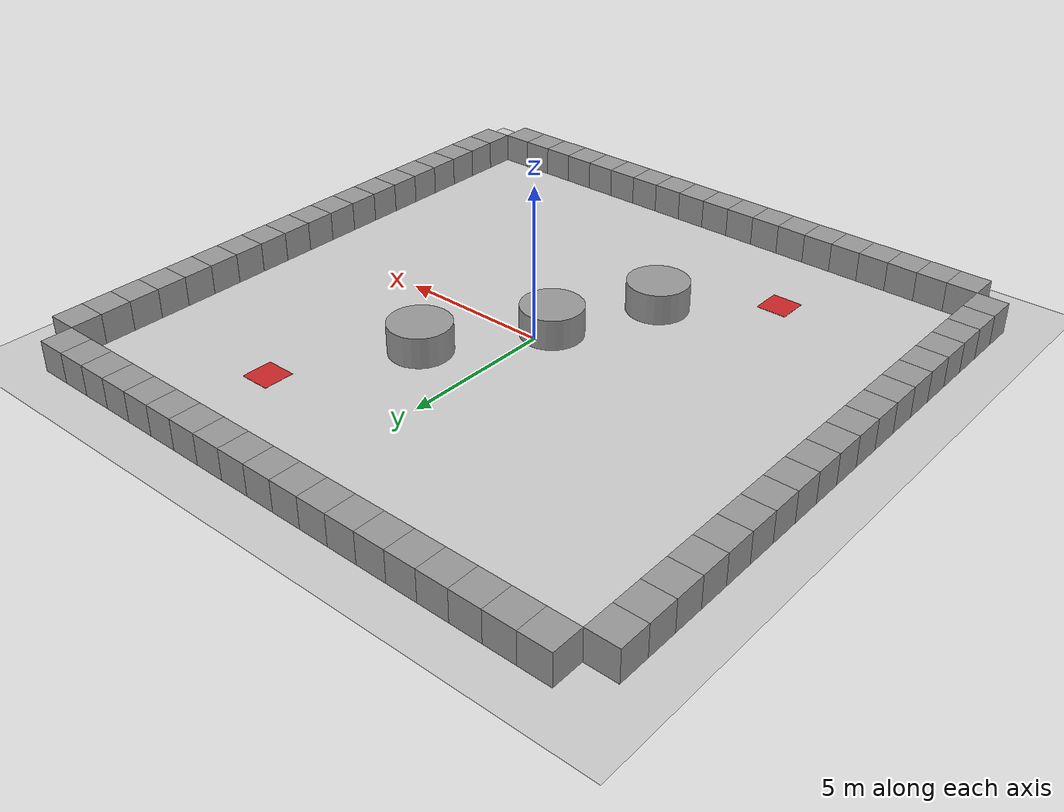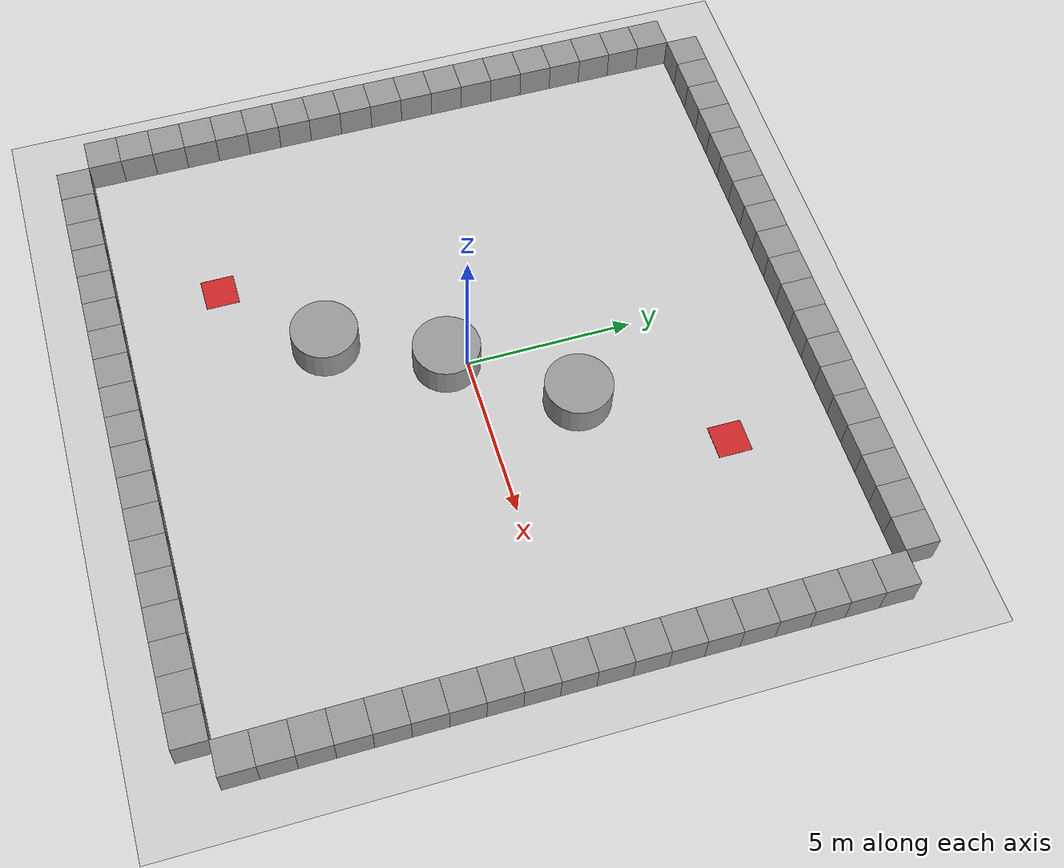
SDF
<sdf version="1.6">
 <world name="default">
  <light name="sun" type="directional">
   <pose>0 0 10 0 -0 0</pose>
   <diffuse>0.8 0.8 0.8 1</diffuse>
   <specular>0.1 0.1 0.1 1</specular>
   <attenuation>
    <range>1000</range>
    <constant>0.9</constant>
    <linear>0.01</linear>
    <quadratic>0.001</quadratic>
   </attenuation>
   <direction>-0.5 0.5 -1</direction>
  </light>
  <model name="ground_plane">
   <static>1</static>
   <link name="link">
    <collision name="collision">
     <geometry><plane><normal>0 0 1</normal><size>100 100</size></plane></geometry>
     <surface><friction><ode><mu>100</mu><mu2>50</mu2></ode></friction></surface>
    </collision>
    <visual name="visual">
     <cast_shadows>0</cast_shadows>
     <geometry><plane><normal>0 0 1</normal><size>100 100</size></plane></geometry>
     <material>
      <script><uri>file://media/materials/scripts/gazebo.material</uri><name>Gazebo/Grey</name></script>
     </material>
    </visual>
   </link>
  </model>
  <physics name="default_physics" default="0" type="ode">
   <real_time_update_rate>1000</real_time_update_rate>
   <max_step_size>0.001</max_step_size>
   <real_time_factor>1</real_time_factor>
   <ode>
    <solver>
     <type>quick</type>
     <iters>150</iters>
     <precon_iters>0</precon_iters>
     <sor>1.4</sor>
     <use_dynamic_moi_rescaling>1</use_dynamic_moi_rescaling>
    </solver>
    <constraints>
     <cfm>1e-05</cfm>
     <erp>0.2</erp>
     <contact_max_correcting_vel>2000</contact_max_correcting_vel>
     <contact_surface_layer>0.01</contact_surface_layer>
    </constraints>
   </ode>
  </physics>
  <gravity>0 0 -9.8</gravity>
  <magnetic_field>6e-06 2.3e-05 -4.2e-05</magnetic_field>
  <atmosphere type="adiabatic"/>
  <scene><ambient>0.4 0.4 0.4 1</ambient><background>0.7 0.7 0.7 1</background><shadows>1</shadows></scene>
  <spherical_coordinates>
   <surface_model>EARTH_WGS84</surface_model>
   <latitude_deg>0</latitude_deg>
   <longitude_deg>0</longitude_deg>
   <elevation>0</elevation>
   <heading_deg>0</heading_deg>
  </spherical_coordinates>
  <model name="wall3">
   <link name="link">
    <inertial>
     <mass>1</mass>
     <inertia>
      <ixx>0.166667</ixx>
      <ixy>0</ixy>
      <ixz>0</ixz>
      <iyy>0.166667</iyy>
      <iyz>0</iyz>
      <izz>0.166667</izz>
     </inertia>
    </inertial>
    <visual name="visual">
     <geometry><box><size>1 1 1</size></box></geometry>
     <material>
      <script><name>Gazebo/Grey</name><uri>file://media/materials/scripts/gazebo.material</uri></script>
      <ambient>0.3 0.3 0.3 1</ambient>
      <diffuse>0.7 0.7 0.7 1</diffuse>
      <specular>0.01 0.01 0.01 1</specular>
      <emissive>0 0 0 1</emissive>
     </material>
    </visual>
    <collision name="collision">
     <geometry><box><size>1 1 1</size></box></geometry>
     <surface>
      <friction>
       <ode><mu>1</mu><mu2>1</mu2><fdir1>0 0 0</fdir1><slip1>0</slip1><slip2>0</slip2></ode>
       <torsional>
        <coefficient>1</coefficient>
        <patch_radius>0</patch_radius>
        <surface_radius>0</surface_radius>
        <use_patch_radius>1</use_patch_radius>
        <ode><slip>0</slip></ode>
       </torsional>
      </friction>
      <bounce><restitution_coefficient>0</restitution_coefficient><threshold>1e+06</threshold></bounce>
      <contact>
       <collide_without_contact>0</collide_without_contact>
       <collide_without_contact_bitmask>1</collide_without_contact_bitmask>
       <collide_bitmask>1</collide_bitmask>
       <ode>
        <soft_cfm>0</soft_cfm>
        <soft_erp>0.2</soft_erp>
        <kp>1e+13</kp>
        <kd>1</kd>
        <max_vel>0.01</max_vel>
        <min_depth>0</min_depth>
       </ode>
       <bullet>
        <split_impulse>1</split_impulse>
        <split_impulse_penetration_threshold>-0.01</split_impulse_penetration_threshold>
        <soft_cfm>0</soft_cfm>
        <soft_erp>0.2</soft_erp>
        <kp>1e+13</kp>
        <kd>1</kd>
       </bullet>
      </contact>
     </surface>
    </collision>
   </link>
   <link name="link_10">
    <pose>0 -4 0 0 -0 0</pose>
    <inertial>
     <mass>1</mass>
     <inertia>
      <ixx>0.166667</ixx>
      <ixy>0</ixy>
      <ixz>0</ixz>
      <iyy>0.166667</iyy>
      <iyz>0</iyz>
      <izz>0.166667</izz>
     </inertia>
    </inertial>
    <visual name="visual">
     <geometry><box><size>1 1 1</size></box></geometry>
     <material>
      <lighting>1</lighting>
      <script><uri>file://media/materials/scripts/gazebo.material</uri><name>Gazebo/Grey</name></script>
      <ambient>0.3 0.3 0.3 1</ambient>
      <diffuse>0.7 0.7 0.7 1</diffuse>
      <specular>0.01 0.01 0.01 1</specular>
      <emissive>0 0 0 1</emissive>
     </material>
    </visual>
    <collision name="collision">
     <geometry><box><size>1 1 1</size></box></geometry>
     <surface>
      <friction>
       <ode><mu>1</mu><mu2>1</mu2><fdir1>0 0 0</fdir1><slip1>0</slip1><slip2>0</slip2></ode>
       <torsional>
        <coefficient>1</coefficient>
        <patch_radius>0</patch_radius>
        <surface_radius>0</surface_radius>
        <use_patch_radius>1</use_patch_radius>
        <ode><slip>0</slip></ode>
       </torsional>
      </friction>
      <bounce><restitution_coefficient>0</restitution_coefficient><threshold>1e+06</threshold></bounce>
      <contact>
       <collide_without_contact>0</collide_without_contact>
       <collide_without_contact_bitmask>1</collide_without_contact_bitmask>
       <collide_bitmask>1</collide_bitmask>
       <ode>
        <soft_cfm>0</soft_cfm>
        <soft_erp>0.2</soft_erp>
        <kp>1e+13</kp>
        <kd>1</kd>
        <max_vel>0.01</max_vel>
        <min_depth>0</min_depth>
       </ode>
       <bullet>
        <split_impulse>1</split_impulse>
        <split_impulse_penetration_threshold>-0.01</split_impulse_penetration_threshold>
        <soft_cfm>0</soft_cfm>
        <soft_erp>0.2</soft_erp>
        <kp>1e+13</kp>
        <kd>1</kd>
       </bullet>
      </contact>
     </surface>
    </collision>
   </link>
   <link name="link_11">
    <pose>0 -5 0 0 -0 0</pose>
    <inertial>
     <mass>1</mass>
     <inertia>
      <ixx>0.166667</ixx>
      <ixy>0</ixy>
      <ixz>0</ixz>
      <iyy>0.166667</iyy>
      <iyz>0</iyz>
      <izz>0.166667</izz>
     </inertia>
    </inertial>
    <visual name="visual">
     <geometry><box><size>1 1 1</size></box></geometry>
     <material>
      <lighting>1</lighting>
      <script><uri>file://media/materials/scripts/gazebo.material</uri><name>Gazebo/Grey</name></script>
      <ambient>0.3 0.3 0.3 1</ambient>
      <diffuse>0.7 0.7 0.7 1</diffuse>
      <specular>0.01 0.01 0.01 1</specular>
      <emissive>0 0 0 1</emissive>
     </material>
    </visual>
    <collision name="collision">
     <geometry><box><size>1 1 1</size></box></geometry>
     <surface>
      <friction>
       <ode><mu>1</mu><mu2>1</mu2><fdir1>0 0 0</fdir1><slip1>0</slip1><slip2>0</slip2></ode>
       <torsional>
        <coefficient>1</coefficient>
        <patch_radius>0</patch_radius>
        <surface_radius>0</surface_radius>
        <use_patch_radius>1</use_patch_radius>
        <ode><slip>0</slip></ode>
       </torsional>
      </friction>
      <bounce><restitution_coefficient>0</restitution_coefficient><threshold>1e+06</threshold></bounce>
      <contact>
       <collide_without_contact>0</collide_without_contact>
       <collide_without_contact_bitmask>1</collide_without_contact_bitmask>
       <collide_bitmask>1</collide_bitmask>
       <ode>
        <soft_cfm>0</soft_cfm>
        <soft_erp>0.2</soft_erp>
        <kp>1e+13</kp>
        <kd>1</kd>
        <max_vel>0.01</max_vel>
        <min_depth>0</min_depth>
       </ode>
       <bullet>
        <split_impulse>1</split_impulse>
        <split_impulse_penetration_threshold>-0.01</split_impulse_penetration_threshold>
        <soft_cfm>0</soft_cfm>
        <soft_erp>0.2</soft_erp>
        <kp>1e+13</kp>
        <kd>1</kd>
       </bullet>
      </contact>
     </surface>
    </collision>
   </link>
   <link name="link_12">
    <pose>0 -6 0 0 -0 0</pose>
    <inertial>
     <mass>1</mass>
     <inertia>
      <ixx>0.166667</ixx>
      <ixy>0</ixy>
      <ixz>0</ixz>
      <iyy>0.166667</iyy>
      <iyz>0</iyz>
      <izz>0.166667</izz>
     </inertia>
    </inertial>
    <visual name="visual">
     <geometry><box><size>1 1 1</size></box></geometry>
     <material>
      <lighting>1</lighting>
      <script><uri>file://media/materials/scripts/gazebo.material</uri><name>Gazebo/Grey</name></script>
      <ambient>0.3 0.3 0.3 1</ambient>
      <diffuse>0.7 0.7 0.7 1</diffuse>
      <specular>0.01 0.01 0.01 1</specular>
      <emissive>0 0 0 1</emissive>
     </material>
    </visual>
    <collision name="collision">
     <geometry><box><size>1 1 1</size></box></geometry>
     <surface>
      <friction>
       <ode><mu>1</mu><mu2>1</mu2><fdir1>0 0 0</fdir1><slip1>0</slip1><slip2>0</slip2></ode>
       <torsional>
        <coefficient>1</coefficient>
        <patch_radius>0</patch_radius>
        <surface_radius>0</surface_radius>
        <use_patch_radius>1</use_patch_radius>
        <ode><slip>0</slip></ode>
       </torsional>
      </friction>
      <bounce><restitution_coefficient>0</restitution_coefficient><threshold>1e+06</threshold></bounce>
      <contact>
       <collide_without_contact>0</collide_without_contact>
       <collide_without_contact_bitmask>1</collide_without_contact_bitmask>
       <collide_bitmask>1</collide_bitmask>
       <ode>
        <soft_cfm>0</soft_cfm>
        <soft_erp>0.2</soft_erp>
        <kp>1e+13</kp>
        <kd>1</kd>
        <max_vel>0.01</max_vel>
        <min_depth>0</min_depth>
       </ode>
       <bullet>
        <split_impulse>1</split_impulse>
        <split_impulse_penetration_threshold>-0.01</split_impulse_penetration_threshold>
        <soft_cfm>0</soft_cfm>
        <soft_erp>0.2</soft_erp>
        <kp>1e+13</kp>
        <kd>1</kd>
       </bullet>
      </contact>
     </surface>
    </collision>
   </link>
   <link name="link_13">
    <pose>0 -7 0 0 -0 0</pose>
    <inertial>
     <mass>1</mass>
     <inertia>
      <ixx>0.166667</ixx>
      <ixy>0</ixy>
      <ixz>0</ixz>
      <iyy>0.166667</iyy>
      <iyz>0</iyz>
      <izz>0.166667</izz>
     </inertia>
    </inertial>
    <visual name="visual">
     <geometry><box><size>1 1 1</size></box></geometry>
     <material>
      <lighting>1</lighting>
      <script><uri>file://media/materials/scripts/gazebo.material</uri><name>Gazebo/Grey</name></script>
      <ambient>0.3 0.3 0.3 1</ambient>
      <diffuse>0.7 0.7 0.7 1</diffuse>
      <specular>0.01 0.01 0.01 1</specular>
      <emissive>0 0 0 1</emissive>
     </material>
    </visual>
    <collision name="collision">
     <geometry><box><size>1 1 1</size></box></geometry>
     <surface>
      <friction>
       <ode><mu>1</mu><mu2>1</mu2><fdir1>0 0 0</fdir1><slip1>0</slip1><slip2>0</slip2></ode>
       <torsional>
        <coefficient>1</coefficient>
        <patch_radius>0</patch_radius>
        <surface_radius>0</surface_radius>
        <use_patch_radius>1</use_patch_radius>
        <ode><slip>0</slip></ode>
       </torsional>
      </friction>
      <bounce><restitution_coefficient>0</restitution_coefficient><threshold>1e+06</threshold></bounce>
      <contact>
       <collide_without_contact>0</collide_without_contact>
       <collide_without_contact_bitmask>1</collide_without_contact_bitmask>
       <collide_bitmask>1</collide_bitmask>
       <ode>
        <soft_cfm>0</soft_cfm>
        <soft_erp>0.2</soft_erp>
        <kp>1e+13</kp>
        <kd>1</kd>
        <max_vel>0.01</max_vel>
        <min_depth>0</min_depth>
       </ode>
       <bullet>
        <split_impulse>1</split_impulse>
        <split_impulse_penetration_threshold>-0.01</split_impulse_penetration_threshold>
        <soft_cfm>0</soft_cfm>
        <soft_erp>0.2</soft_erp>
        <kp>1e+13</kp>
        <kd>1</kd>
       </bullet>
      </contact>
     </surface>
    </collision>
   </link>
   <link name="link_14">
    <pose>0 -8 0 0 -0 0</pose>
    <inertial>
     <mass>1</mass>
     <inertia>
      <ixx>0.166667</ixx>
      <ixy>0</ixy>
      <ixz>0</ixz>
      <iyy>0.166667</iyy>
      <iyz>0</iyz>
      <izz>0.166667</izz>
     </inertia>
    </inertial>
    <visual name="visual">
     <geometry><box><size>1 1 1</size></box></geometry>
     <material>
      <lighting>1</lighting>
      <script><uri>file://media/materials/scripts/gazebo.material</uri><name>Gazebo/Grey</name></script>
      <ambient>0.3 0.3 0.3 1</ambient>
      <diffuse>0.7 0.7 0.7 1</diffuse>
      <specular>0.01 0.01 0.01 1</specular>
      <emissive>0 0 0 1</emissive>
     </material>
    </visual>
    <collision name="collision">
     <geometry><box><size>1 1 1</size></box></geometry>
     <surface>
      <friction>
       <ode><mu>1</mu><mu2>1</mu2><fdir1>0 0 0</fdir1><slip1>0</slip1><slip2>0</slip2></ode>
       <torsional>
        <coefficient>1</coefficient>
        <patch_radius>0</patch_radius>
        <surface_radius>0</surface_radius>
        <use_patch_radius>1</use_patch_radius>
        <ode><slip>0</slip></ode>
       </torsional>
      </friction>
      <bounce><restitution_coefficient>0</restitution_coefficient><threshold>1e+06</threshold></bounce>
      <contact>
       <collide_without_contact>0</collide_without_contact>
       <collide_without_contact_bitmask>1</collide_without_contact_bitmask>
       <collide_bitmask>1</collide_bitmask>
       <ode>
        <soft_cfm>0</soft_cfm>
        <soft_erp>0.2</soft_erp>
        <kp>1e+13</kp>
        <kd>1</kd>
        <max_vel>0.01</max_vel>
        <min_depth>0</min_depth>
       </ode>
       <bullet>
        <split_impulse>1</split_impulse>
        <split_impulse_penetration_threshold>-0.01</split_impulse_penetration_threshold>
        <soft_cfm>0</soft_cfm>
        <soft_erp>0.2</soft_erp>
        <kp>1e+13</kp>
        <kd>1</kd>
       </bullet>
      </contact>
     </surface>
    </collision>
   </link>
   <link name="link_15">
    <pose>0 1 0 0 -0 0</pose>
    <inertial>
     <mass>1</mass>
     <inertia>
      <ixx>0.166667</ixx>
      <ixy>0</ixy>
      <ixz>0</ixz>
      <iyy>0.166667</iyy>
      <iyz>0</iyz>
      <izz>0.166667</izz>
     </inertia>
    </inertial>
    <visual name="visual">
     <geometry><box><size>1 1 1</size></box></geometry>
     <material>
      <lighting>1</lighting>
      <script><uri>file://media/materials/scripts/gazebo.material</uri><name>Gazebo/Grey</name></script>
      <ambient>0.3 0.3 0.3 1</ambient>
      <diffuse>0.7 0.7 0.7 1</diffuse>
      <specular>0.01 0.01 0.01 1</specular>
      <emissive>0 0 0 1</emissive>
     </material>
    </visual>
    <collision name="collision">
     <geometry><box><size>1 1 1</size></box></geometry>
     <surface>
      <friction>
       <ode><mu>1</mu><mu2>1</mu2><fdir1>0 0 0</fdir1><slip1>0</slip1><slip2>0</slip2></ode>
       <torsional>
        <coefficient>1</coefficient>
        <patch_radius>0</patch_radius>
        <surface_radius>0</surface_radius>
        <use_patch_radius>1</use_patch_radius>
        <ode><slip>0</slip></ode>
       </torsional>
      </friction>
      <bounce><restitution_coefficient>0</restitution_coefficient><threshold>1e+06</threshold></bounce>
      <contact>
       <collide_without_contact>0</collide_without_contact>
       <collide_without_contact_bitmask>1</collide_without_contact_bitmask>
       <collide_bitmask>1</collide_bitmask>
       <ode>
        <soft_cfm>0</soft_cfm>
        <soft_erp>0.2</soft_erp>
        <kp>1e+13</kp>
        <kd>1</kd>
        <max_vel>0.01</max_vel>
        <min_depth>0</min_depth>
       </ode>
       <bullet>
        <split_impulse>1</split_impulse>
        <split_impulse_penetration_threshold>-0.01</split_impulse_penetration_threshold>
        <soft_cfm>0</soft_cfm>
        <soft_erp>0.2</soft_erp>
        <kp>1e+13</kp>
        <kd>1</kd>
       </bullet>
      </contact>
     </surface>
    </collision>
   </link>
   <link name="link_16">
    <pose>0 2 0 0 -0 0</pose>
    <inertial>
     <mass>1</mass>
     <inertia>
      <ixx>0.166667</ixx>
      <ixy>0</ixy>
      <ixz>0</ixz>
      <iyy>0.166667</iyy>
      <iyz>0</iyz>
      <izz>0.166667</izz>
     </inertia>
    </inertial>
    <visual name="visual">
     <geometry><box><size>1 1 1</size></box></geometry>
     <material>
      <lighting>1</lighting>
      <script><uri>file://media/materials/scripts/gazebo.material</uri><name>Gazebo/Grey</name></script>
      <ambient>0.3 0.3 0.3 1</ambient>
      <diffuse>0.7 0.7 0.7 1</diffuse>
      <specular>0.01 0.01 0.01 1</specular>
      <emissive>0 0 0 1</emissive>
     </material>
    </visual>
    <collision name="collision">
     <geometry><box><size>1 1 1</size></box></geometry>
     <surface>
      <friction>
       <ode><mu>1</mu><mu2>1</mu2><fdir1>0 0 0</fdir1><slip1>0</slip1><slip2>0</slip2></ode>
       <torsional>
        <coefficient>1</coefficient>
        <patch_radius>0</patch_radius>
        <surface_radius>0</surface_radius>
        <use_patch_radius>1</use_patch_radius>
        <ode><slip>0</slip></ode>
       </torsional>
      </friction>
      <bounce><restitution_coefficient>0</restitution_coefficient><threshold>1e+06</threshold></bounce>
      <contact>
       <collide_without_contact>0</collide_without_contact>
       <collide_without_contact_bitmask>1</collide_without_contact_bitmask>
       <collide_bitmask>1</collide_bitmask>
       <ode>
        <soft_cfm>0</soft_cfm>
        <soft_erp>0.2</soft_erp>
        <kp>1e+13</kp>
        <kd>1</kd>
        <max_vel>0.01</max_vel>
        <min_depth>0</min_depth>
       </ode>
       <bullet>
        <split_impulse>1</split_impulse>
        <split_impulse_penetration_threshold>-0.01</split_impulse_penetration_threshold>
        <soft_cfm>0</soft_cfm>
        <soft_erp>0.2</soft_erp>
        <kp>1e+13</kp>
        <kd>1</kd>
       </bullet>
      </contact>
     </surface>
    </collision>
   </link>
   <link name="link_17">
    <pose>0 3 0 0 -0 0</pose>
    <inertial>
     <mass>1</mass>
     <inertia>
      <ixx>0.166667</ixx>
      <ixy>0</ixy>
      <ixz>0</ixz>
      <iyy>0.166667</iyy>
      <iyz>0</iyz>
      <izz>0.166667</izz>
     </inertia>
    </inertial>
    <visual name="visual">
     <geometry><box><size>1 1 1</size></box></geometry>
     <material>
      <lighting>1</lighting>
      <script><uri>file://media/materials/scripts/gazebo.material</uri><name>Gazebo/Grey</name></script>
      <ambient>0.3 0.3 0.3 1</ambient>
      <diffuse>0.7 0.7 0.7 1</diffuse>
      <specular>0.01 0.01 0.01 1</specular>
      <emissive>0 0 0 1</emissive>
     </material>
    </visual>
    <collision name="collision">
     <geometry><box><size>1 1 1</size></box></geometry>
     <surface>
      <friction>
       <ode><mu>1</mu><mu2>1</mu2><fdir1>0 0 0</fdir1><slip1>0</slip1><slip2>0</slip2></ode>
       <torsional>
        <coefficient>1</coefficient>
        <patch_radius>0</patch_radius>
        <surface_radius>0</surface_radius>
        <use_patch_radius>1</use_patch_radius>
        <ode><slip>0</slip></ode>
       </torsional>
      </friction>
      <bounce><restitution_coefficient>0</restitution_coefficient><threshold>1e+06</threshold></bounce>
      <contact>
       <collide_without_contact>0</collide_without_contact>
       <collide_without_contact_bitmask>1</collide_without_contact_bitmask>
       <collide_bitmask>1</collide_bitmask>
       <ode>
        <soft_cfm>0</soft_cfm>
        <soft_erp>0.2</soft_erp>
        <kp>1e+13</kp>
        <kd>1</kd>
        <max_vel>0.01</max_vel>
        <min_depth>0</min_depth>
       </ode>
       <bullet>
        <split_impulse>1</split_impulse>
        <split_impulse_penetration_threshold>-0.01</split_impulse_penetration_threshold>
        <soft_cfm>0</soft_cfm>
        <soft_erp>0.2</soft_erp>
        <kp>1e+13</kp>
        <kd>1</kd>
       </bullet>
      </contact>
     </surface>
    </collision>
   </link>
   <link name="link_18">
    <pose>0 4 0 0 -0 0</pose>
    <inertial>
     <mass>1</mass>
     <inertia>
      <ixx>0.166667</ixx>
      <ixy>0</ixy>
      <ixz>0</ixz>
      <iyy>0.166667</iyy>
      <iyz>0</iyz>
      <izz>0.166667</izz>
     </inertia>
    </inertial>
    <visual name="visual">
     <geometry><box><size>1 1 1</size></box></geometry>
     <material>
      <lighting>1</lighting>
      <script><uri>file://media/materials/scripts/gazebo.material</uri><name>Gazebo/Grey</name></script>
      <ambient>0.3 0.3 0.3 1</ambient>
      <diffuse>0.7 0.7 0.7 1</diffuse>
      <specular>0.01 0.01 0.01 1</specular>
      <emissive>0 0 0 1</emissive>
     </material>
    </visual>
    <collision name="collision">
     <geometry><box><size>1 1 1</size></box></geometry>
     <surface>
      <friction>
       <ode><mu>1</mu><mu2>1</mu2><fdir1>0 0 0</fdir1><slip1>0</slip1><slip2>0</slip2></ode>
       <torsional>
        <coefficient>1</coefficient>
        <patch_radius>0</patch_radius>
        <surface_radius>0</surface_radius>
        <use_patch_radius>1</use_patch_radius>
        <ode><slip>0</slip></ode>
       </torsional>
      </friction>
      <bounce><restitution_coefficient>0</restitution_coefficient><threshold>1e+06</threshold></bounce>
      <contact>
       <collide_without_contact>0</collide_without_contact>
       <collide_without_contact_bitmask>1</collide_without_contact_bitmask>
       <collide_bitmask>1</collide_bitmask>
       <ode>
        <soft_cfm>0</soft_cfm>
        <soft_erp>0.2</soft_erp>
        <kp>1e+13</kp>
        <kd>1</kd>
        <max_vel>0.01</max_vel>
        <min_depth>0</min_depth>
       </ode>
       <bullet>
        <split_impulse>1</split_impulse>
        <split_impulse_penetration_threshold>-0.01</split_impulse_penetration_threshold>
        <soft_cfm>0</soft_cfm>
        <soft_erp>0.2</soft_erp>
        <kp>1e+13</kp>
        <kd>1</kd>
       </bullet>
      </contact>
     </surface>
    </collision>
   </link>
   <link name="link_19">
    <pose>0 5 0 0 -0 0</pose>
    <inertial>
     <mass>1</mass>
     <inertia>
      <ixx>0.166667</ixx>
      <ixy>0</ixy>
      <ixz>0</ixz>
      <iyy>0.166667</iyy>
      <iyz>0</iyz>
      <izz>0.166667</izz>
     </inertia>
    </inertial>
    <visual name="visual">
     <geometry><box><size>1 1 1</size></box></geometry>
     <material>
      <lighting>1</lighting>
      <script><uri>file://media/materials/scripts/gazebo.material</uri><name>Gazebo/Grey</name></script>
      <ambient>0.3 0.3 0.3 1</ambient>
      <diffuse>0.7 0.7 0.7 1</diffuse>
      <specular>0.01 0.01 0.01 1</specular>
      <emissive>0 0 0 1</emissive>
     </material>
    </visual>
    <collision name="collision">
     <geometry><box><size>1 1 1</size></box></geometry>
     <surface>
      <friction>
       <ode><mu>1</mu><mu2>1</mu2><fdir1>0 0 0</fdir1><slip1>0</slip1><slip2>0</slip2></ode>
       <torsional>
        <coefficient>1</coefficient>
        <patch_radius>0</patch_radius>
        <surface_radius>0</surface_radius>
        <use_patch_radius>1</use_patch_radius>
        <ode><slip>0</slip></ode>
       </torsional>
      </friction>
      <bounce><restitution_coefficient>0</restitution_coefficient><threshold>1e+06</threshold></bounce>
      <contact>
       <collide_without_contact>0</collide_without_contact>
       <collide_without_contact_bitmask>1</collide_without_contact_bitmask>
       <collide_bitmask>1</collide_bitmask>
       <ode>
        <soft_cfm>0</soft_cfm>
        <soft_erp>0.2</soft_erp>
        <kp>1e+13</kp>
        <kd>1</kd>
        <max_vel>0.01</max_vel>
        <min_depth>0</min_depth>
       </ode>
       <bullet>
        <split_impulse>1</split_impulse>
        <split_impulse_penetration_threshold>-0.01</split_impulse_penetration_threshold>
        <soft_cfm>0</soft_cfm>
        <soft_erp>0.2</soft_erp>
        <kp>1e+13</kp>
        <kd>1</kd>
       </bullet>
      </contact>
     </surface>
    </collision>
   </link>
   <link name="link_20">
    <pose>0 6 0 0 -0 0</pose>
    <inertial>
     <mass>1</mass>
     <inertia>
      <ixx>0.166667</ixx>
      <ixy>0</ixy>
      <ixz>0</ixz>
      <iyy>0.166667</iyy>
      <iyz>0</iyz>
      <izz>0.166667</izz>
     </inertia>
    </inertial>
    <visual name="visual">
     <geometry><box><size>1 1 1</size></box></geometry>
     <material>
      <lighting>1</lighting>
      <script><uri>file://media/materials/scripts/gazebo.material</uri><name>Gazebo/Grey</name></script>
      <ambient>0.3 0.3 0.3 1</ambient>
      <diffuse>0.7 0.7 0.7 1</diffuse>
      <specular>0.01 0.01 0.01 1</specular>
      <emissive>0 0 0 1</emissive>
     </material>
    </visual>
    <collision name="collision">
     <geometry><box><size>1 1 1</size></box></geometry>
     <surface>
      <friction>
       <ode><mu>1</mu><mu2>1</mu2><fdir1>0 0 0</fdir1><slip1>0</slip1><slip2>0</slip2></ode>
       <torsional>
        <coefficient>1</coefficient>
        <patch_radius>0</patch_radius>
        <surface_radius>0</surface_radius>
        <use_patch_radius>1</use_patch_radius>
        <ode><slip>0</slip></ode>
       </torsional>
      </friction>
      <bounce><restitution_coefficient>0</restitution_coefficient><threshold>1e+06</threshold></bounce>
      <contact>
       <collide_without_contact>0</collide_without_contact>
       <collide_without_contact_bitmask>1</collide_without_contact_bitmask>
       <collide_bitmask>1</collide_bitmask>
       <ode>
        <soft_cfm>0</soft_cfm>
        <soft_erp>0.2</soft_erp>
        <kp>1e+13</kp>
        <kd>1</kd>
        <max_vel>0.01</max_vel>
        <min_depth>0</min_depth>
       </ode>
       <bullet>
        <split_impulse>1</split_impulse>
        <split_impulse_penetration_threshold>-0.01</split_impulse_penetration_threshold>
        <soft_cfm>0</soft_cfm>
        <soft_erp>0.2</soft_erp>
        <kp>1e+13</kp>
        <kd>1</kd>
       </bullet>
      </contact>
     </surface>
    </collision>
   </link>
   <link name="link_21">
    <pose>0 7 0 0 -0 0</pose>
    <inertial>
     <mass>1</mass>
     <inertia>
      <ixx>0.166667</ixx>
      <ixy>0</ixy>
      <ixz>0</ixz>
      <iyy>0.166667</iyy>
      <iyz>0</iyz>
      <izz>0.166667</izz>
     </inertia>
    </inertial>
    <visual name="visual">
     <geometry><box><size>1 1 1</size></box></geometry>
     <material>
      <lighting>1</lighting>
      <script><uri>file://media/materials/scripts/gazebo.material</uri><name>Gazebo/Grey</name></script>
      <ambient>0.3 0.3 0.3 1</ambient>
      <diffuse>0.7 0.7 0.7 1</diffuse>
      <specular>0.01 0.01 0.01 1</specular>
      <emissive>0 0 0 1</emissive>
     </material>
    </visual>
    <collision name="collision">
     <geometry><box><size>1 1 1</size></box></geometry>
     <surface>
      <friction>
       <ode><mu>1</mu><mu2>1</mu2><fdir1>0 0 0</fdir1><slip1>0</slip1><slip2>0</slip2></ode>
       <torsional>
        <coefficient>1</coefficient>
        <patch_radius>0</patch_radius>
        <surface_radius>0</surface_radius>
        <use_patch_radius>1</use_patch_radius>
        <ode><slip>0</slip></ode>
       </torsional>
      </friction>
      <bounce><restitution_coefficient>0</restitution_coefficient><threshold>1e+06</threshold></bounce>
      <contact>
       <collide_without_contact>0</collide_without_contact>
       <collide_without_contact_bitmask>1</collide_without_contact_bitmask>
       <collide_bitmask>1</collide_bitmask>
       <ode>
        <soft_cfm>0</soft_cfm>
        <soft_erp>0.2</soft_erp>
        <kp>1e+13</kp>
        <kd>1</kd>
        <max_vel>0.01</max_vel>
        <min_depth>0</min_depth>
       </ode>
       <bullet>
        <split_impulse>1</split_impulse>
        <split_impulse_penetration_threshold>-0.01</split_impulse_penetration_threshold>
        <soft_cfm>0</soft_cfm>
        <soft_erp>0.2</soft_erp>
        <kp>1e+13</kp>
        <kd>1</kd>
       </bullet>
      </contact>
     </surface>
    </collision>
   </link>
   <link name="link_22">
    <pose>0 8 0 0 -0 0</pose>
    <inertial>
     <mass>1</mass>
     <inertia>
      <ixx>0.166667</ixx>
      <ixy>0</ixy>
      <ixz>0</ixz>
      <iyy>0.166667</iyy>
      <iyz>0</iyz>
      <izz>0.166667</izz>
     </inertia>
    </inertial>
    <visual name="visual">
     <geometry><box><size>1 1 1</size></box></geometry>
     <material>
      <lighting>1</lighting>
      <script><uri>file://media/materials/scripts/gazebo.material</uri><name>Gazebo/Grey</name></script>
      <ambient>0.3 0.3 0.3 1</ambient>
      <diffuse>0.7 0.7 0.7 1</diffuse>
      <specular>0.01 0.01 0.01 1</specular>
      <emissive>0 0 0 1</emissive>
     </material>
    </visual>
    <collision name="collision">
     <geometry><box><size>1 1 1</size></box></geometry>
     <surface>
      <friction>
       <ode><mu>1</mu><mu2>1</mu2><fdir1>0 0 0</fdir1><slip1>0</slip1><slip2>0</slip2></ode>
       <torsional>
        <coefficient>1</coefficient>
        <patch_radius>0</patch_radius>
        <surface_radius>0</surface_radius>
        <use_patch_radius>1</use_patch_radius>
        <ode><slip>0</slip></ode>
       </torsional>
      </friction>
      <bounce><restitution_coefficient>0</restitution_coefficient><threshold>1e+06</threshold></bounce>
      <contact>
       <collide_without_contact>0</collide_without_contact>
       <collide_without_contact_bitmask>1</collide_without_contact_bitmask>
       <collide_bitmask>1</collide_bitmask>
       <ode>
        <soft_cfm>0</soft_cfm>
        <soft_erp>0.2</soft_erp>
        <kp>1e+13</kp>
        <kd>1</kd>
        <max_vel>0.01</max_vel>
        <min_depth>0</min_depth>
       </ode>
       <bullet>
        <split_impulse>1</split_impulse>
        <split_impulse_penetration_threshold>-0.01</split_impulse_penetration_threshold>
        <soft_cfm>0</soft_cfm>
        <soft_erp>0.2</soft_erp>
        <kp>1e+13</kp>
        <kd>1</kd>
       </bullet>
      </contact>
     </surface>
    </collision>
   </link>
   <link name="link_23">
    <pose>0 9 0 0 -0 0</pose>
    <inertial>
     <mass>1</mass>
     <inertia>
      <ixx>0.166667</ixx>
      <ixy>0</ixy>
      <ixz>0</ixz>
      <iyy>0.166667</iyy>
      <iyz>0</iyz>
      <izz>0.166667</izz>
     </inertia>
    </inertial>
    <visual name="visual">
     <geometry><box><size>1 1 1</size></box></geometry>
     <material>
      <lighting>1</lighting>
      <script><uri>file://media/materials/scripts/gazebo.material</uri><name>Gazebo/Grey</name></script>
      <ambient>0.3 0.3 0.3 1</ambient>
      <diffuse>0.7 0.7 0.7 1</diffuse>
      <specular>0.01 0.01 0.01 1</specular>
      <emissive>0 0 0 1</emissive>
     </material>
    </visual>
    <collision name="collision">
     <geometry><box><size>1 1 1</size></box></geometry>
     <surface>
      <friction>
       <ode><mu>1</mu><mu2>1</mu2><fdir1>0 0 0</fdir1><slip1>0</slip1><slip2>0</slip2></ode>
       <torsional>
        <coefficient>1</coefficient>
        <patch_radius>0</patch_radius>
        <surface_radius>0</surface_radius>
        <use_patch_radius>1</use_patch_radius>
        <ode><slip>0</slip></ode>
       </torsional>
      </friction>
      <bounce><restitution_coefficient>0</restitution_coefficient><threshold>1e+06</threshold></bounce>
      <contact>
       <collide_without_contact>0</collide_without_contact>
       <collide_without_contact_bitmask>1</collide_without_contact_bitmask>
       <collide_bitmask>1</collide_bitmask>
       <ode>
        <soft_cfm>0</soft_cfm>
        <soft_erp>0.2</soft_erp>
        <kp>1e+13</kp>
        <kd>1</kd>
        <max_vel>0.01</max_vel>
        <min_depth>0</min_depth>
       </ode>
       <bullet>
        <split_impulse>1</split_impulse>
        <split_impulse_penetration_threshold>-0.01</split_impulse_penetration_threshold>
        <soft_cfm>0</soft_cfm>
        <soft_erp>0.2</soft_erp>
        <kp>1e+13</kp>
        <kd>1</kd>
       </bullet>
      </contact>
     </surface>
    </collision>
   </link>
   <link name="link_24">
    <pose>0 -9 0 0 -0 0</pose>
    <inertial>
     <mass>1</mass>
     <inertia>
      <ixx>0.166667</ixx>
      <ixy>0</ixy>
      <ixz>0</ixz>
      <iyy>0.166667</iyy>
      <iyz>0</iyz>
      <izz>0.166667</izz>
     </inertia>
    </inertial>
    <visual name="visual">
     <geometry><box><size>1 1 1</size></box></geometry>
     <material>
      <lighting>1</lighting>
      <script><uri>file://media/materials/scripts/gazebo.material</uri><name>Gazebo/Grey</name></script>
      <ambient>0.3 0.3 0.3 1</ambient>
      <diffuse>0.7 0.7 0.7 1</diffuse>
      <specular>0.01 0.01 0.01 1</specular>
      <emissive>0 0 0 1</emissive>
     </material>
    </visual>
    <collision name="collision">
     <geometry><box><size>1 1 1</size></box></geometry>
     <surface>
      <friction>
       <ode><mu>1</mu><mu2>1</mu2><fdir1>0 0 0</fdir1><slip1>0</slip1><slip2>0</slip2></ode>
       <torsional>
        <coefficient>1</coefficient>
        <patch_radius>0</patch_radius>
        <surface_radius>0</surface_radius>
        <use_patch_radius>1</use_patch_radius>
        <ode><slip>0</slip></ode>
       </torsional>
      </friction>
      <bounce><restitution_coefficient>0</restitution_coefficient><threshold>1e+06</threshold></bounce>
      <contact>
       <collide_without_contact>0</collide_without_contact>
       <collide_without_contact_bitmask>1</collide_without_contact_bitmask>
       <collide_bitmask>1</collide_bitmask>
       <ode>
        <soft_cfm>0</soft_cfm>
        <soft_erp>0.2</soft_erp>
        <kp>1e+13</kp>
        <kd>1</kd>
        <max_vel>0.01</max_vel>
        <min_depth>0</min_depth>
       </ode>
       <bullet>
        <split_impulse>1</split_impulse>
        <split_impulse_penetration_threshold>-0.01</split_impulse_penetration_threshold>
        <soft_cfm>0</soft_cfm>
        <soft_erp>0.2</soft_erp>
        <kp>1e+13</kp>
        <kd>1</kd>
       </bullet>
      </contact>
     </surface>
    </collision>
   </link>
   <link name="link_7">
    <pose>0 -1 0 0 -0 0</pose>
    <inertial>
     <mass>1</mass>
     <inertia>
      <ixx>0.166667</ixx>
      <ixy>0</ixy>
      <ixz>0</ixz>
      <iyy>0.166667</iyy>
      <iyz>0</iyz>
      <izz>0.166667</izz>
     </inertia>
    </inertial>
    <visual name="visual">
     <geometry><box><size>1 1 1</size></box></geometry>
     <material>
      <lighting>1</lighting>
      <script><uri>file://media/materials/scripts/gazebo.material</uri><name>Gazebo/Grey</name></script>
      <ambient>0.3 0.3 0.3 1</ambient>
      <diffuse>0.7 0.7 0.7 1</diffuse>
      <specular>0.01 0.01 0.01 1</specular>
      <emissive>0 0 0 1</emissive>
     </material>
    </visual>
    <collision name="collision">
     <geometry><box><size>1 1 1</size></box></geometry>
     <surface>
      <friction>
       <ode><mu>1</mu><mu2>1</mu2><fdir1>0 0 0</fdir1><slip1>0</slip1><slip2>0</slip2></ode>
       <torsional>
        <coefficient>1</coefficient>
        <patch_radius>0</patch_radius>
        <surface_radius>0</surface_radius>
        <use_patch_radius>1</use_patch_radius>
        <ode><slip>0</slip></ode>
       </torsional>
      </friction>
      <bounce><restitution_coefficient>0</restitution_coefficient><threshold>1e+06</threshold></bounce>
      <contact>
       <collide_without_contact>0</collide_without_contact>
       <collide_without_contact_bitmask>1</collide_without_contact_bitmask>
       <collide_bitmask>1</collide_bitmask>
       <ode>
        <soft_cfm>0</soft_cfm>
        <soft_erp>0.2</soft_erp>
        <kp>1e+13</kp>
        <kd>1</kd>
        <max_vel>0.01</max_vel>
        <min_depth>0</min_depth>
       </ode>
       <bullet>
        <split_impulse>1</split_impulse>
        <split_impulse_penetration_threshold>-0.01</split_impulse_penetration_threshold>
        <soft_cfm>0</soft_cfm>
        <soft_erp>0.2</soft_erp>
        <kp>1e+13</kp>
        <kd>1</kd>
       </bullet>
      </contact>
     </surface>
    </collision>
   </link>
   <link name="link_8">
    <pose>0 -2 0 0 -0 0</pose>
    <inertial>
     <mass>1</mass>
     <inertia>
      <ixx>0.166667</ixx>
      <ixy>0</ixy>
      <ixz>0</ixz>
      <iyy>0.166667</iyy>
      <iyz>0</iyz>
      <izz>0.166667</izz>
     </inertia>
    </inertial>
    <visual name="visual">
     <geometry><box><size>1 1 1</size></box></geometry>
     <material>
      <lighting>1</lighting>
      <script><uri>file://media/materials/scripts/gazebo.material</uri><name>Gazebo/Grey</name></script>
      <ambient>0.3 0.3 0.3 1</ambient>
      <diffuse>0.7 0.7 0.7 1</diffuse>
      <specular>0.01 0.01 0.01 1</specular>
      <emissive>0 0 0 1</emissive>
     </material>
    </visual>
    <collision name="collision">
     <geometry><box><size>1 1 1</size></box></geometry>
     <surface>
      <friction>
       <ode><mu>1</mu><mu2>1</mu2><fdir1>0 0 0</fdir1><slip1>0</slip1><slip2>0</slip2></ode>
       <torsional>
        <coefficient>1</coefficient>
        <patch_radius>0</patch_radius>
        <surface_radius>0</surface_radius>
        <use_patch_radius>1</use_patch_radius>
        <ode><slip>0</slip></ode>
       </torsional>
      </friction>
      <bounce><restitution_coefficient>0</restitution_coefficient><threshold>1e+06</threshold></bounce>
      <contact>
       <collide_without_contact>0</collide_without_contact>
       <collide_without_contact_bitmask>1</collide_without_contact_bitmask>
       <collide_bitmask>1</collide_bitmask>
       <ode>
        <soft_cfm>0</soft_cfm>
        <soft_erp>0.2</soft_erp>
        <kp>1e+13</kp>
        <kd>1</kd>
        <max_vel>0.01</max_vel>
        <min_depth>0</min_depth>
       </ode>
       <bullet>
        <split_impulse>1</split_impulse>
        <split_impulse_penetration_threshold>-0.01</split_impulse_penetration_threshold>
        <soft_cfm>0</soft_cfm>
        <soft_erp>0.2</soft_erp>
        <kp>1e+13</kp>
        <kd>1</kd>
       </bullet>
      </contact>
     </surface>
    </collision>
   </link>
   <link name="link_9">
    <pose>0 -3 0 0 -0 0</pose>
    <inertial>
     <mass>1</mass>
     <inertia>
      <ixx>0.166667</ixx>
      <ixy>0</ixy>
      <ixz>0</ixz>
      <iyy>0.166667</iyy>
      <iyz>0</iyz>
      <izz>0.166667</izz>
     </inertia>
    </inertial>
    <visual name="visual">
     <geometry><box><size>1 1 1</size></box></geometry>
     <material>
      <lighting>1</lighting>
      <script><uri>file://media/materials/scripts/gazebo.material</uri><name>Gazebo/Grey</name></script>
      <ambient>0.3 0.3 0.3 1</ambient>
      <diffuse>0.7 0.7 0.7 1</diffuse>
      <specular>0.01 0.01 0.01 1</specular>
      <emissive>0 0 0 1</emissive>
     </material>
    </visual>
    <collision name="collision">
     <geometry><box><size>1 1 1</size></box></geometry>
     <surface>
      <friction>
       <ode><mu>1</mu><mu2>1</mu2><fdir1>0 0 0</fdir1><slip1>0</slip1><slip2>0</slip2></ode>
       <torsional>
        <coefficient>1</coefficient>
        <patch_radius>0</patch_radius>
        <surface_radius>0</surface_radius>
        <use_patch_radius>1</use_patch_radius>
        <ode><slip>0</slip></ode>
       </torsional>
      </friction>
      <bounce><restitution_coefficient>0</restitution_coefficient><threshold>1e+06</threshold></bounce>
      <contact>
       <collide_without_contact>0</collide_without_contact>
       <collide_without_contact_bitmask>1</collide_without_contact_bitmask>
       <collide_bitmask>1</collide_bitmask>
       <ode>
        <soft_cfm>0</soft_cfm>
        <soft_erp>0.2</soft_erp>
        <kp>1e+13</kp>
        <kd>1</kd>
        <max_vel>0.01</max_vel>
        <min_depth>0</min_depth>
       </ode>
       <bullet>
        <split_impulse>1</split_impulse>
        <split_impulse_penetration_threshold>-0.01</split_impulse_penetration_threshold>
        <soft_cfm>0</soft_cfm>
        <soft_erp>0.2</soft_erp>
        <kp>1e+13</kp>
        <kd>1</kd>
       </bullet>
      </contact>
     </surface>
    </collision>
   </link>
   <static>0</static>
   <pose>-10 0 0.5 0 -0 0</pose>
  </model>
  <model name="wall4">
   <link name="link">
    <inertial>
     <mass>1</mass>
     <inertia>
      <ixx>0.166667</ixx>
      <ixy>0</ixy>
      <ixz>0</ixz>
      <iyy>0.166667</iyy>
      <iyz>0</iyz>
      <izz>0.166667</izz>
     </inertia>
    </inertial>
    <visual name="visual">
     <geometry><box><size>1 1 1</size></box></geometry>
     <material>
      <script><name>Gazebo/Grey</name><uri>file://media/materials/scripts/gazebo.material</uri></script>
      <ambient>0.3 0.3 0.3 1</ambient>
      <diffuse>0.7 0.7 0.7 1</diffuse>
      <specular>0.01 0.01 0.01 1</specular>
      <emissive>0 0 0 1</emissive>
     </material>
    </visual>
    <collision name="collision">
     <geometry><box><size>1 1 1</size></box></geometry>
     <surface>
      <friction>
       <ode><mu>1</mu><mu2>1</mu2><fdir1>0 0 0</fdir1><slip1>0</slip1><slip2>0</slip2></ode>
       <torsional>
        <coefficient>1</coefficient>
        <patch_radius>0</patch_radius>
        <surface_radius>0</surface_radius>
        <use_patch_radius>1</use_patch_radius>
        <ode><slip>0</slip></ode>
       </torsional>
      </friction>
      <bounce><restitution_coefficient>0</restitution_coefficient><threshold>1e+06</threshold></bounce>
      <contact>
       <collide_without_contact>0</collide_without_contact>
       <collide_without_contact_bitmask>1</collide_without_contact_bitmask>
       <collide_bitmask>1</collide_bitmask>
       <ode>
        <soft_cfm>0</soft_cfm>
        <soft_erp>0.2</soft_erp>
        <kp>1e+13</kp>
        <kd>1</kd>
        <max_vel>0.01</max_vel>
        <min_depth>0</min_depth>
       </ode>
       <bullet>
        <split_impulse>1</split_impulse>
        <split_impulse_penetration_threshold>-0.01</split_impulse_penetration_threshold>
        <soft_cfm>0</soft_cfm>
        <soft_erp>0.2</soft_erp>
        <kp>1e+13</kp>
        <kd>1</kd>
       </bullet>
      </contact>
     </surface>
    </collision>
   </link>
   <link name="link_25">
    <pose>1 0 0 0 -0 0</pose>
    <inertial>
     <mass>1</mass>
     <inertia>
      <ixx>0.166667</ixx>
      <ixy>0</ixy>
      <ixz>0</ixz>
      <iyy>0.166667</iyy>
      <iyz>0</iyz>
      <izz>0.166667</izz>
     </inertia>
    </inertial>
    <visual name="visual">
     <geometry><box><size>1 1 1</size></box></geometry>
     <material>
      <lighting>1</lighting>
      <script><uri>file://media/materials/scripts/gazebo.material</uri><name>Gazebo/Grey</name></script>
      <ambient>0.3 0.3 0.3 1</ambient>
      <diffuse>0.7 0.7 0.7 1</diffuse>
      <specular>0.01 0.01 0.01 1</specular>
      <emissive>0 0 0 1</emissive>
     </material>
    </visual>
    <collision name="collision">
     <geometry><box><size>1 1 1</size></box></geometry>
     <surface>
      <friction>
       <ode><mu>1</mu><mu2>1</mu2><fdir1>0 0 0</fdir1><slip1>0</slip1><slip2>0</slip2></ode>
       <torsional>
        <coefficient>1</coefficient>
        <patch_radius>0</patch_radius>
        <surface_radius>0</surface_radius>
        <use_patch_radius>1</use_patch_radius>
        <ode><slip>0</slip></ode>
       </torsional>
      </friction>
      <bounce><restitution_coefficient>0</restitution_coefficient><threshold>1e+06</threshold></bounce>
      <contact>
       <collide_without_contact>0</collide_without_contact>
       <collide_without_contact_bitmask>1</collide_without_contact_bitmask>
       <collide_bitmask>1</collide_bitmask>
       <ode>
        <soft_cfm>0</soft_cfm>
        <soft_erp>0.2</soft_erp>
        <kp>1e+13</kp>
        <kd>1</kd>
        <max_vel>0.01</max_vel>
        <min_depth>0</min_depth>
       </ode>
       <bullet>
        <split_impulse>1</split_impulse>
        <split_impulse_penetration_threshold>-0.01</split_impulse_penetration_threshold>
        <soft_cfm>0</soft_cfm>
        <soft_erp>0.2</soft_erp>
        <kp>1e+13</kp>
        <kd>1</kd>
       </bullet>
      </contact>
     </surface>
    </collision>
   </link>
   <link name="link_26">
    <pose>2 0 0 0 -0 0</pose>
    <inertial>
     <mass>1</mass>
     <inertia>
      <ixx>0.166667</ixx>
      <ixy>0</ixy>
      <ixz>0</ixz>
      <iyy>0.166667</iyy>
      <iyz>0</iyz>
      <izz>0.166667</izz>
     </inertia>
    </inertial>
    <visual name="visual">
     <geometry><box><size>1 1 1</size></box></geometry>
     <material>
      <lighting>1</lighting>
      <script><uri>file://media/materials/scripts/gazebo.material</uri><name>Gazebo/Grey</name></script>
      <ambient>0.3 0.3 0.3 1</ambient>
      <diffuse>0.7 0.7 0.7 1</diffuse>
      <specular>0.01 0.01 0.01 1</specular>
      <emissive>0 0 0 1</emissive>
     </material>
    </visual>
    <collision name="collision">
     <geometry><box><size>1 1 1</size></box></geometry>
     <surface>
      <friction>
       <ode><mu>1</mu><mu2>1</mu2><fdir1>0 0 0</fdir1><slip1>0</slip1><slip2>0</slip2></ode>
       <torsional>
        <coefficient>1</coefficient>
        <patch_radius>0</patch_radius>
        <surface_radius>0</surface_radius>
        <use_patch_radius>1</use_patch_radius>
        <ode><slip>0</slip></ode>
       </torsional>
      </friction>
      <bounce><restitution_coefficient>0</restitution_coefficient><threshold>1e+06</threshold></bounce>
      <contact>
       <collide_without_contact>0</collide_without_contact>
       <collide_without_contact_bitmask>1</collide_without_contact_bitmask>
       <collide_bitmask>1</collide_bitmask>
       <ode>
        <soft_cfm>0</soft_cfm>
        <soft_erp>0.2</soft_erp>
        <kp>1e+13</kp>
        <kd>1</kd>
        <max_vel>0.01</max_vel>
        <min_depth>0</min_depth>
       </ode>
       <bullet>
        <split_impulse>1</split_impulse>
        <split_impulse_penetration_threshold>-0.01</split_impulse_penetration_threshold>
        <soft_cfm>0</soft_cfm>
        <soft_erp>0.2</soft_erp>
        <kp>1e+13</kp>
        <kd>1</kd>
       </bullet>
      </contact>
     </surface>
    </collision>
   </link>
   <link name="link_27">
    <pose>3 0 0 0 -0 0</pose>
    <inertial>
     <mass>1</mass>
     <inertia>
      <ixx>0.166667</ixx>
      <ixy>0</ixy>
      <ixz>0</ixz>
      <iyy>0.166667</iyy>
      <iyz>0</iyz>
      <izz>0.166667</izz>
     </inertia>
    </inertial>
    <visual name="visual">
     <geometry><box><size>1 1 1</size></box></geometry>
     <material>
      <lighting>1</lighting>
      <script><uri>file://media/materials/scripts/gazebo.material</uri><name>Gazebo/Grey</name></script>
      <ambient>0.3 0.3 0.3 1</ambient>
      <diffuse>0.7 0.7 0.7 1</diffuse>
      <specular>0.01 0.01 0.01 1</specular>
      <emissive>0 0 0 1</emissive>
     </material>
    </visual>
    <collision name="collision">
     <geometry><box><size>1 1 1</size></box></geometry>
     <surface>
      <friction>
       <ode><mu>1</mu><mu2>1</mu2><fdir1>0 0 0</fdir1><slip1>0</slip1><slip2>0</slip2></ode>
       <torsional>
        <coefficient>1</coefficient>
        <patch_radius>0</patch_radius>
        <surface_radius>0</surface_radius>
        <use_patch_radius>1</use_patch_radius>
        <ode><slip>0</slip></ode>
       </torsional>
      </friction>
      <bounce><restitution_coefficient>0</restitution_coefficient><threshold>1e+06</threshold></bounce>
      <contact>
       <collide_without_contact>0</collide_without_contact>
       <collide_without_contact_bitmask>1</collide_without_contact_bitmask>
       <collide_bitmask>1</collide_bitmask>
       <ode>
        <soft_cfm>0</soft_cfm>
        <soft_erp>0.2</soft_erp>
        <kp>1e+13</kp>
        <kd>1</kd>
        <max_vel>0.01</max_vel>
        <min_depth>0</min_depth>
       </ode>
       <bullet>
        <split_impulse>1</split_impulse>
        <split_impulse_penetration_threshold>-0.01</split_impulse_penetration_threshold>
        <soft_cfm>0</soft_cfm>
        <soft_erp>0.2</soft_erp>
        <kp>1e+13</kp>
        <kd>1</kd>
       </bullet>
      </contact>
     </surface>
    </collision>
   </link>
   <link name="link_28">
    <pose>4 0 0 0 -0 0</pose>
    <inertial>
     <mass>1</mass>
     <inertia>
      <ixx>0.166667</ixx>
      <ixy>0</ixy>
      <ixz>0</ixz>
      <iyy>0.166667</iyy>
      <iyz>0</iyz>
      <izz>0.166667</izz>
     </inertia>
    </inertial>
    <visual name="visual">
     <geometry><box><size>1 1 1</size></box></geometry>
     <material>
      <lighting>1</lighting>
      <script><uri>file://media/materials/scripts/gazebo.material</uri><name>Gazebo/Grey</name></script>
      <ambient>0.3 0.3 0.3 1</ambient>
      <diffuse>0.7 0.7 0.7 1</diffuse>
      <specular>0.01 0.01 0.01 1</specular>
      <emissive>0 0 0 1</emissive>
     </material>
    </visual>
    <collision name="collision">
     <geometry><box><size>1 1 1</size></box></geometry>
     <surface>
      <friction>
       <ode><mu>1</mu><mu2>1</mu2><fdir1>0 0 0</fdir1><slip1>0</slip1><slip2>0</slip2></ode>
       <torsional>
        <coefficient>1</coefficient>
        <patch_radius>0</patch_radius>
        <surface_radius>0</surface_radius>
        <use_patch_radius>1</use_patch_radius>
        <ode><slip>0</slip></ode>
       </torsional>
      </friction>
      <bounce><restitution_coefficient>0</restitution_coefficient><threshold>1e+06</threshold></bounce>
      <contact>
       <collide_without_contact>0</collide_without_contact>
       <collide_without_contact_bitmask>1</collide_without_contact_bitmask>
       <collide_bitmask>1</collide_bitmask>
       <ode>
        <soft_cfm>0</soft_cfm>
        <soft_erp>0.2</soft_erp>
        <kp>1e+13</kp>
        <kd>1</kd>
        <max_vel>0.01</max_vel>
        <min_depth>0</min_depth>
       </ode>
       <bullet>
        <split_impulse>1</split_impulse>
        <split_impulse_penetration_threshold>-0.01</split_impulse_penetration_threshold>
        <soft_cfm>0</soft_cfm>
        <soft_erp>0.2</soft_erp>
        <kp>1e+13</kp>
        <kd>1</kd>
       </bullet>
      </contact>
     </surface>
    </collision>
   </link>
   <link name="link_29">
    <pose>5 0 0 0 -0 0</pose>
    <inertial>
     <mass>1</mass>
     <inertia>
      <ixx>0.166667</ixx>
      <ixy>0</ixy>
      <ixz>0</ixz>
      <iyy>0.166667</iyy>
      <iyz>0</iyz>
      <izz>0.166667</izz>
     </inertia>
    </inertial>
    <visual name="visual">
     <geometry><box><size>1 1 1</size></box></geometry>
     <material>
      <lighting>1</lighting>
      <script><uri>file://media/materials/scripts/gazebo.material</uri><name>Gazebo/Grey</name></script>
      <ambient>0.3 0.3 0.3 1</ambient>
      <diffuse>0.7 0.7 0.7 1</diffuse>
      <specular>0.01 0.01 0.01 1</specular>
      <emissive>0 0 0 1</emissive>
     </material>
    </visual>
    <collision name="collision">
     <geometry><box><size>1 1 1</size></box></geometry>
     <surface>
      <friction>
       <ode><mu>1</mu><mu2>1</mu2><fdir1>0 0 0</fdir1><slip1>0</slip1><slip2>0</slip2></ode>
       <torsional>
        <coefficient>1</coefficient>
        <patch_radius>0</patch_radius>
        <surface_radius>0</surface_radius>
        <use_patch_radius>1</use_patch_radius>
        <ode><slip>0</slip></ode>
       </torsional>
      </friction>
      <bounce><restitution_coefficient>0</restitution_coefficient><threshold>1e+06</threshold></bounce>
      <contact>
       <collide_without_contact>0</collide_without_contact>
       <collide_without_contact_bitmask>1</collide_without_contact_bitmask>
       <collide_bitmask>1</collide_bitmask>
       <ode>
        <soft_cfm>0</soft_cfm>
        <soft_erp>0.2</soft_erp>
        <kp>1e+13</kp>
        <kd>1</kd>
        <max_vel>0.01</max_vel>
        <min_depth>0</min_depth>
       </ode>
       <bullet>
        <split_impulse>1</split_impulse>
        <split_impulse_penetration_threshold>-0.01</split_impulse_penetration_threshold>
        <soft_cfm>0</soft_cfm>
        <soft_erp>0.2</soft_erp>
        <kp>1e+13</kp>
        <kd>1</kd>
       </bullet>
      </contact>
     </surface>
    </collision>
   </link>
   <link name="link_30">
    <pose>6 0 0 0 -0 0</pose>
    <inertial>
     <mass>1</mass>
     <inertia>
      <ixx>0.166667</ixx>
      <ixy>0</ixy>
      <ixz>0</ixz>
      <iyy>0.166667</iyy>
      <iyz>0</iyz>
      <izz>0.166667</izz>
     </inertia>
    </inertial>
    <visual name="visual">
     <geometry><box><size>1 1 1</size></box></geometry>
     <material>
      <lighting>1</lighting>
      <script><uri>file://media/materials/scripts/gazebo.material</uri><name>Gazebo/Grey</name></script>
      <ambient>0.3 0.3 0.3 1</ambient>
      <diffuse>0.7 0.7 0.7 1</diffuse>
      <specular>0.01 0.01 0.01 1</specular>
      <emissive>0 0 0 1</emissive>
     </material>
    </visual>
    <collision name="collision">
     <geometry><box><size>1 1 1</size></box></geometry>
     <surface>
      <friction>
       <ode><mu>1</mu><mu2>1</mu2><fdir1>0 0 0</fdir1><slip1>0</slip1><slip2>0</slip2></ode>
       <torsional>
        <coefficient>1</coefficient>
        <patch_radius>0</patch_radius>
        <surface_radius>0</surface_radius>
        <use_patch_radius>1</use_patch_radius>
        <ode><slip>0</slip></ode>
       </torsional>
      </friction>
      <bounce><restitution_coefficient>0</restitution_coefficient><threshold>1e+06</threshold></bounce>
      <contact>
       <collide_without_contact>0</collide_without_contact>
       <collide_without_contact_bitmask>1</collide_without_contact_bitmask>
       <collide_bitmask>1</collide_bitmask>
       <ode>
        <soft_cfm>0</soft_cfm>
        <soft_erp>0.2</soft_erp>
        <kp>1e+13</kp>
        <kd>1</kd>
        <max_vel>0.01</max_vel>
        <min_depth>0</min_depth>
       </ode>
       <bullet>
        <split_impulse>1</split_impulse>
        <split_impulse_penetration_threshold>-0.01</split_impulse_penetration_threshold>
        <soft_cfm>0</soft_cfm>
        <soft_erp>0.2</soft_erp>
        <kp>1e+13</kp>
        <kd>1</kd>
       </bullet>
      </contact>
     </surface>
    </collision>
   </link>
   <link name="link_31">
    <pose>7 0 0 0 -0 0</pose>
    <inertial>
     <mass>1</mass>
     <inertia>
      <ixx>0.166667</ixx>
      <ixy>0</ixy>
      <ixz>0</ixz>
      <iyy>0.166667</iyy>
      <iyz>0</iyz>
      <izz>0.166667</izz>
     </inertia>
    </inertial>
    <visual name="visual">
     <geometry><box><size>1 1 1</size></box></geometry>
     <material>
      <lighting>1</lighting>
      <script><uri>file://media/materials/scripts/gazebo.material</uri><name>Gazebo/Grey</name></script>
      <ambient>0.3 0.3 0.3 1</ambient>
      <diffuse>0.7 0.7 0.7 1</diffuse>
      <specular>0.01 0.01 0.01 1</specular>
      <emissive>0 0 0 1</emissive>
     </material>
    </visual>
    <collision name="collision">
     <geometry><box><size>1 1 1</size></box></geometry>
     <surface>
      <friction>
       <ode><mu>1</mu><mu2>1</mu2><fdir1>0 0 0</fdir1><slip1>0</slip1><slip2>0</slip2></ode>
       <torsional>
        <coefficient>1</coefficient>
        <patch_radius>0</patch_radius>
        <surface_radius>0</surface_radius>
        <use_patch_radius>1</use_patch_radius>
        <ode><slip>0</slip></ode>
       </torsional>
      </friction>
      <bounce><restitution_coefficient>0</restitution_coefficient><threshold>1e+06</threshold></bounce>
      <contact>
       <collide_without_contact>0</collide_without_contact>
       <collide_without_contact_bitmask>1</collide_without_contact_bitmask>
       <collide_bitmask>1</collide_bitmask>
       <ode>
        <soft_cfm>0</soft_cfm>
        <soft_erp>0.2</soft_erp>
        <kp>1e+13</kp>
        <kd>1</kd>
        <max_vel>0.01</max_vel>
        <min_depth>0</min_depth>
       </ode>
       <bullet>
        <split_impulse>1</split_impulse>
        <split_impulse_penetration_threshold>-0.01</split_impulse_penetration_threshold>
        <soft_cfm>0</soft_cfm>
        <soft_erp>0.2</soft_erp>
        <kp>1e+13</kp>
        <kd>1</kd>
       </bullet>
      </contact>
     </surface>
    </collision>
   </link>
   <link name="link_32">
    <pose>8 0 0 0 -0 0</pose>
    <inertial>
     <mass>1</mass>
     <inertia>
      <ixx>0.166667</ixx>
      <ixy>0</ixy>
      <ixz>0</ixz>
      <iyy>0.166667</iyy>
      <iyz>0</iyz>
      <izz>0.166667</izz>
     </inertia>
    </inertial>
    <visual name="visual">
     <geometry><box><size>1 1 1</size></box></geometry>
     <material>
      <lighting>1</lighting>
      <script><uri>file://media/materials/scripts/gazebo.material</uri><name>Gazebo/Grey</name></script>
      <ambient>0.3 0.3 0.3 1</ambient>
      <diffuse>0.7 0.7 0.7 1</diffuse>
      <specular>0.01 0.01 0.01 1</specular>
      <emissive>0 0 0 1</emissive>
     </material>
    </visual>
    <collision name="collision">
     <geometry><box><size>1 1 1</size></box></geometry>
     <surface>
      <friction>
       <ode><mu>1</mu><mu2>1</mu2><fdir1>0 0 0</fdir1><slip1>0</slip1><slip2>0</slip2></ode>
       <torsional>
        <coefficient>1</coefficient>
        <patch_radius>0</patch_radius>
        <surface_radius>0</surface_radius>
        <use_patch_radius>1</use_patch_radius>
        <ode><slip>0</slip></ode>
       </torsional>
      </friction>
      <bounce><restitution_coefficient>0</restitution_coefficient><threshold>1e+06</threshold></bounce>
      <contact>
       <collide_without_contact>0</collide_without_contact>
       <collide_without_contact_bitmask>1</collide_without_contact_bitmask>
       <collide_bitmask>1</collide_bitmask>
       <ode>
        <soft_cfm>0</soft_cfm>
        <soft_erp>0.2</soft_erp>
        <kp>1e+13</kp>
        <kd>1</kd>
        <max_vel>0.01</max_vel>
        <min_depth>0</min_depth>
       </ode>
       <bullet>
        <split_impulse>1</split_impulse>
        <split_impulse_penetration_threshold>-0.01</split_impulse_penetration_threshold>
        <soft_cfm>0</soft_cfm>
        <soft_erp>0.2</soft_erp>
        <kp>1e+13</kp>
        <kd>1</kd>
       </bullet>
      </contact>
     </surface>
    </collision>
   </link>
   <link name="link_33">
    <pose>9 0 0 0 -0 0</pose>
    <inertial>
     <mass>1</mass>
     <inertia>
      <ixx>0.166667</ixx>
      <ixy>0</ixy>
      <ixz>0</ixz>
      <iyy>0.166667</iyy>
      <iyz>0</iyz>
      <izz>0.166667</izz>
     </inertia>
    </inertial>
    <visual name="visual">
     <geometry><box><size>1 1 1</size></box></geometry>
     <material>
      <lighting>1</lighting>
      <script><uri>file://media/materials/scripts/gazebo.material</uri><name>Gazebo/Grey</name></script>
      <ambient>0.3 0.3 0.3 1</ambient>
      <diffuse>0.7 0.7 0.7 1</diffuse>
      <specular>0.01 0.01 0.01 1</specular>
      <emissive>0 0 0 1</emissive>
     </material>
    </visual>
    <collision name="collision">
     <geometry><box><size>1 1 1</size></box></geometry>
     <surface>
      <friction>
       <ode><mu>1</mu><mu2>1</mu2><fdir1>0 0 0</fdir1><slip1>0</slip1><slip2>0</slip2></ode>
       <torsional>
        <coefficient>1</coefficient>
        <patch_radius>0</patch_radius>
        <surface_radius>0</surface_radius>
        <use_patch_radius>1</use_patch_radius>
        <ode><slip>0</slip></ode>
       </torsional>
      </friction>
      <bounce><restitution_coefficient>0</restitution_coefficient><threshold>1e+06</threshold></bounce>
      <contact>
       <collide_without_contact>0</collide_without_contact>
       <collide_without_contact_bitmask>1</collide_without_contact_bitmask>
       <collide_bitmask>1</collide_bitmask>
       <ode>
        <soft_cfm>0</soft_cfm>
        <soft_erp>0.2</soft_erp>
        <kp>1e+13</kp>
        <kd>1</kd>
        <max_vel>0.01</max_vel>
        <min_depth>0</min_depth>
       </ode>
       <bullet>
        <split_impulse>1</split_impulse>
        <split_impulse_penetration_threshold>-0.01</split_impulse_penetration_threshold>
        <soft_cfm>0</soft_cfm>
        <soft_erp>0.2</soft_erp>
        <kp>1e+13</kp>
        <kd>1</kd>
       </bullet>
      </contact>
     </surface>
    </collision>
   </link>
   <link name="link_34">
    <pose>-1 0 0 0 -0 0</pose>
    <inertial>
     <mass>1</mass>
     <inertia>
      <ixx>0.166667</ixx>
      <ixy>0</ixy>
      <ixz>0</ixz>
      <iyy>0.166667</iyy>
      <iyz>0</iyz>
      <izz>0.166667</izz>
     </inertia>
    </inertial>
    <visual name="visual">
     <geometry><box><size>1 1 1</size></box></geometry>
     <material>
      <lighting>1</lighting>
      <script><uri>file://media/materials/scripts/gazebo.material</uri><name>Gazebo/Grey</name></script>
      <ambient>0.3 0.3 0.3 1</ambient>
      <diffuse>0.7 0.7 0.7 1</diffuse>
      <specular>0.01 0.01 0.01 1</specular>
      <emissive>0 0 0 1</emissive>
     </material>
    </visual>
    <collision name="collision">
     <geometry><box><size>1 1 1</size></box></geometry>
     <surface>
      <friction>
       <ode><mu>1</mu><mu2>1</mu2><fdir1>0 0 0</fdir1><slip1>0</slip1><slip2>0</slip2></ode>
       <torsional>
        <coefficient>1</coefficient>
        <patch_radius>0</patch_radius>
        <surface_radius>0</surface_radius>
        <use_patch_radius>1</use_patch_radius>
        <ode><slip>0</slip></ode>
       </torsional>
      </friction>
      <bounce><restitution_coefficient>0</restitution_coefficient><threshold>1e+06</threshold></bounce>
      <contact>
       <collide_without_contact>0</collide_without_contact>
       <collide_without_contact_bitmask>1</collide_without_contact_bitmask>
       <collide_bitmask>1</collide_bitmask>
       <ode>
        <soft_cfm>0</soft_cfm>
        <soft_erp>0.2</soft_erp>
        <kp>1e+13</kp>
        <kd>1</kd>
        <max_vel>0.01</max_vel>
        <min_depth>0</min_depth>
       </ode>
       <bullet>
        <split_impulse>1</split_impulse>
        <split_impulse_penetration_threshold>-0.01</split_impulse_penetration_threshold>
        <soft_cfm>0</soft_cfm>
        <soft_erp>0.2</soft_erp>
        <kp>1e+13</kp>
        <kd>1</kd>
       </bullet>
      </contact>
     </surface>
    </collision>
   </link>
   <link name="link_35">
    <pose>-2 0 0 0 -0 0</pose>
    <inertial>
     <mass>1</mass>
     <inertia>
      <ixx>0.166667</ixx>
      <ixy>0</ixy>
      <ixz>0</ixz>
      <iyy>0.166667</iyy>
      <iyz>0</iyz>
      <izz>0.166667</izz>
     </inertia>
    </inertial>
    <visual name="visual">
     <geometry><box><size>1 1 1</size></box></geometry>
     <material>
      <lighting>1</lighting>
      <script><uri>file://media/materials/scripts/gazebo.material</uri><name>Gazebo/Grey</name></script>
      <ambient>0.3 0.3 0.3 1</ambient>
      <diffuse>0.7 0.7 0.7 1</diffuse>
      <specular>0.01 0.01 0.01 1</specular>
      <emissive>0 0 0 1</emissive>
     </material>
    </visual>
    <collision name="collision">
     <geometry><box><size>1 1 1</size></box></geometry>
     <surface>
      <friction>
       <ode><mu>1</mu><mu2>1</mu2><fdir1>0 0 0</fdir1><slip1>0</slip1><slip2>0</slip2></ode>
       <torsional>
        <coefficient>1</coefficient>
        <patch_radius>0</patch_radius>
        <surface_radius>0</surface_radius>
        <use_patch_radius>1</use_patch_radius>
        <ode><slip>0</slip></ode>
       </torsional>
      </friction>
      <bounce><restitution_coefficient>0</restitution_coefficient><threshold>1e+06</threshold></bounce>
      <contact>
       <collide_without_contact>0</collide_without_contact>
       <collide_without_contact_bitmask>1</collide_without_contact_bitmask>
       <collide_bitmask>1</collide_bitmask>
       <ode>
        <soft_cfm>0</soft_cfm>
        <soft_erp>0.2</soft_erp>
        <kp>1e+13</kp>
        <kd>1</kd>
        <max_vel>0.01</max_vel>
        <min_depth>0</min_depth>
       </ode>
       <bullet>
        <split_impulse>1</split_impulse>
        <split_impulse_penetration_threshold>-0.01</split_impulse_penetration_threshold>
        <soft_cfm>0</soft_cfm>
        <soft_erp>0.2</soft_erp>
        <kp>1e+13</kp>
        <kd>1</kd>
       </bullet>
      </contact>
     </surface>
    </collision>
   </link>
   <link name="link_36">
    <pose>-3 0 0 0 -0 0</pose>
    <inertial>
     <mass>1</mass>
     <inertia>
      <ixx>0.166667</ixx>
      <ixy>0</ixy>
      <ixz>0</ixz>
      <iyy>0.166667</iyy>
      <iyz>0</iyz>
      <izz>0.166667</izz>
     </inertia>
    </inertial>
    <visual name="visual">
     <geometry><box><size>1 1 1</size></box></geometry>
     <material>
      <lighting>1</lighting>
      <script><uri>file://media/materials/scripts/gazebo.material</uri><name>Gazebo/Grey</name></script>
      <ambient>0.3 0.3 0.3 1</ambient>
      <diffuse>0.7 0.7 0.7 1</diffuse>
      <specular>0.01 0.01 0.01 1</specular>
      <emissive>0 0 0 1</emissive>
     </material>
    </visual>
    <collision name="collision">
     <geometry><box><size>1 1 1</size></box></geometry>
     <surface>
      <friction>
       <ode><mu>1</mu><mu2>1</mu2><fdir1>0 0 0</fdir1><slip1>0</slip1><slip2>0</slip2></ode>
       <torsional>
        <coefficient>1</coefficient>
        <patch_radius>0</patch_radius>
        <surface_radius>0</surface_radius>
        <use_patch_radius>1</use_patch_radius>
        <ode><slip>0</slip></ode>
       </torsional>
      </friction>
      <bounce><restitution_coefficient>0</restitution_coefficient><threshold>1e+06</threshold></bounce>
      <contact>
       <collide_without_contact>0</collide_without_contact>
       <collide_without_contact_bitmask>1</collide_without_contact_bitmask>
       <collide_bitmask>1</collide_bitmask>
       <ode>
        <soft_cfm>0</soft_cfm>
        <soft_erp>0.2</soft_erp>
        <kp>1e+13</kp>
        <kd>1</kd>
        <max_vel>0.01</max_vel>
        <min_depth>0</min_depth>
       </ode>
       <bullet>
        <split_impulse>1</split_impulse>
        <split_impulse_penetration_threshold>-0.01</split_impulse_penetration_threshold>
        <soft_cfm>0</soft_cfm>
        <soft_erp>0.2</soft_erp>
        <kp>1e+13</kp>
        <kd>1</kd>
       </bullet>
      </contact>
     </surface>
    </collision>
   </link>
   <link name="link_37">
    <pose>-4 0 0 0 -0 0</pose>
    <inertial>
     <mass>1</mass>
     <inertia>
      <ixx>0.166667</ixx>
      <ixy>0</ixy>
      <ixz>0</ixz>
      <iyy>0.166667</iyy>
      <iyz>0</iyz>
      <izz>0.166667</izz>
     </inertia>
    </inertial>
    <visual name="visual">
     <geometry><box><size>1 1 1</size></box></geometry>
     <material>
      <lighting>1</lighting>
      <script><uri>file://media/materials/scripts/gazebo.material</uri><name>Gazebo/Grey</name></script>
      <ambient>0.3 0.3 0.3 1</ambient>
      <diffuse>0.7 0.7 0.7 1</diffuse>
      <specular>0.01 0.01 0.01 1</specular>
      <emissive>0 0 0 1</emissive>
     </material>
    </visual>
    <collision name="collision">
     <geometry><box><size>1 1 1</size></box></geometry>
     <surface>
      <friction>
       <ode><mu>1</mu><mu2>1</mu2><fdir1>0 0 0</fdir1><slip1>0</slip1><slip2>0</slip2></ode>
       <torsional>
        <coefficient>1</coefficient>
        <patch_radius>0</patch_radius>
        <surface_radius>0</surface_radius>
        <use_patch_radius>1</use_patch_radius>
        <ode><slip>0</slip></ode>
       </torsional>
      </friction>
      <bounce><restitution_coefficient>0</restitution_coefficient><threshold>1e+06</threshold></bounce>
      <contact>
       <collide_without_contact>0</collide_without_contact>
       <collide_without_contact_bitmask>1</collide_without_contact_bitmask>
       <collide_bitmask>1</collide_bitmask>
       <ode>
        <soft_cfm>0</soft_cfm>
        <soft_erp>0.2</soft_erp>
        <kp>1e+13</kp>
        <kd>1</kd>
        <max_vel>0.01</max_vel>
        <min_depth>0</min_depth>
       </ode>
       <bullet>
        <split_impulse>1</split_impulse>
        <split_impulse_penetration_threshold>-0.01</split_impulse_penetration_threshold>
        <soft_cfm>0</soft_cfm>
        <soft_erp>0.2</soft_erp>
        <kp>1e+13</kp>
        <kd>1</kd>
       </bullet>
      </contact>
     </surface>
    </collision>
   </link>
   <link name="link_38">
    <pose>-5 0 0 0 -0 0</pose>
    <inertial>
     <mass>1</mass>
     <inertia>
      <ixx>0.166667</ixx>
      <ixy>0</ixy>
      <ixz>0</ixz>
      <iyy>0.166667</iyy>
      <iyz>0</iyz>
      <izz>0.166667</izz>
     </inertia>
    </inertial>
    <visual name="visual">
     <geometry><box><size>1 1 1</size></box></geometry>
     <material>
      <lighting>1</lighting>
      <script><uri>file://media/materials/scripts/gazebo.material</uri><name>Gazebo/Grey</name></script>
      <ambient>0.3 0.3 0.3 1</ambient>
      <diffuse>0.7 0.7 0.7 1</diffuse>
      <specular>0.01 0.01 0.01 1</specular>
      <emissive>0 0 0 1</emissive>
     </material>
    </visual>
    <collision name="collision">
     <geometry><box><size>1 1 1</size></box></geometry>
     <surface>
      <friction>
       <ode><mu>1</mu><mu2>1</mu2><fdir1>0 0 0</fdir1><slip1>0</slip1><slip2>0</slip2></ode>
       <torsional>
        <coefficient>1</coefficient>
        <patch_radius>0</patch_radius>
        <surface_radius>0</surface_radius>
        <use_patch_radius>1</use_patch_radius>
        <ode><slip>0</slip></ode>
       </torsional>
      </friction>
      <bounce><restitution_coefficient>0</restitution_coefficient><threshold>1e+06</threshold></bounce>
      <contact>
       <collide_without_contact>0</collide_without_contact>
       <collide_without_contact_bitmask>1</collide_without_contact_bitmask>
       <collide_bitmask>1</collide_bitmask>
       <ode>
        <soft_cfm>0</soft_cfm>
        <soft_erp>0.2</soft_erp>
        <kp>1e+13</kp>
        <kd>1</kd>
        <max_vel>0.01</max_vel>
        <min_depth>0</min_depth>
       </ode>
       <bullet>
        <split_impulse>1</split_impulse>
        <split_impulse_penetration_threshold>-0.01</split_impulse_penetration_threshold>
        <soft_cfm>0</soft_cfm>
        <soft_erp>0.2</soft_erp>
        <kp>1e+13</kp>
        <kd>1</kd>
       </bullet>
      </contact>
     </surface>
    </collision>
   </link>
   <link name="link_39">
    <pose>-6 0 0 0 -0 0</pose>
    <inertial>
     <mass>1</mass>
     <inertia>
      <ixx>0.166667</ixx>
      <ixy>0</ixy>
      <ixz>0</ixz>
      <iyy>0.166667</iyy>
      <iyz>0</iyz>
      <izz>0.166667</izz>
     </inertia>
    </inertial>
    <visual name="visual">
     <geometry><box><size>1 1 1</size></box></geometry>
     <material>
      <lighting>1</lighting>
      <script><uri>file://media/materials/scripts/gazebo.material</uri><name>Gazebo/Grey</name></script>
      <ambient>0.3 0.3 0.3 1</ambient>
      <diffuse>0.7 0.7 0.7 1</diffuse>
      <specular>0.01 0.01 0.01 1</specular>
      <emissive>0 0 0 1</emissive>
     </material>
    </visual>
    <collision name="collision">
     <geometry><box><size>1 1 1</size></box></geometry>
     <surface>
      <friction>
       <ode><mu>1</mu><mu2>1</mu2><fdir1>0 0 0</fdir1><slip1>0</slip1><slip2>0</slip2></ode>
       <torsional>
        <coefficient>1</coefficient>
        <patch_radius>0</patch_radius>
        <surface_radius>0</surface_radius>
        <use_patch_radius>1</use_patch_radius>
        <ode><slip>0</slip></ode>
       </torsional>
      </friction>
      <bounce><restitution_coefficient>0</restitution_coefficient><threshold>1e+06</threshold></bounce>
      <contact>
       <collide_without_contact>0</collide_without_contact>
       <collide_without_contact_bitmask>1</collide_without_contact_bitmask>
       <collide_bitmask>1</collide_bitmask>
       <ode>
        <soft_cfm>0</soft_cfm>
        <soft_erp>0.2</soft_erp>
        <kp>1e+13</kp>
        <kd>1</kd>
        <max_vel>0.01</max_vel>
        <min_depth>0</min_depth>
       </ode>
       <bullet>
        <split_impulse>1</split_impulse>
        <split_impulse_penetration_threshold>-0.01</split_impulse_penetration_threshold>
        <soft_cfm>0</soft_cfm>
        <soft_erp>0.2</soft_erp>
        <kp>1e+13</kp>
        <kd>1</kd>
       </bullet>
      </contact>
     </surface>
    </collision>
   </link>
   <link name="link_40">
    <pose>-7 0 0 0 -0 0</pose>
    <inertial>
     <mass>1</mass>
     <inertia>
      <ixx>0.166667</ixx>
      <ixy>0</ixy>
      <ixz>0</ixz>
      <iyy>0.166667</iyy>
      <iyz>0</iyz>
      <izz>0.166667</izz>
     </inertia>
    </inertial>
    <visual name="visual">
     <geometry><box><size>1 1 1</size></box></geometry>
     <material>
      <lighting>1</lighting>
      <script><uri>file://media/materials/scripts/gazebo.material</uri><name>Gazebo/Grey</name></script>
      <ambient>0.3 0.3 0.3 1</ambient>
      <diffuse>0.7 0.7 0.7 1</diffuse>
      <specular>0.01 0.01 0.01 1</specular>
      <emissive>0 0 0 1</emissive>
     </material>
    </visual>
    <collision name="collision">
     <geometry><box><size>1 1 1</size></box></geometry>
     <surface>
      <friction>
       <ode><mu>1</mu><mu2>1</mu2><fdir1>0 0 0</fdir1><slip1>0</slip1><slip2>0</slip2></ode>
       <torsional>
        <coefficient>1</coefficient>
        <patch_radius>0</patch_radius>
        <surface_radius>0</surface_radius>
        <use_patch_radius>1</use_patch_radius>
        <ode><slip>0</slip></ode>
       </torsional>
      </friction>
      <bounce><restitution_coefficient>0</restitution_coefficient><threshold>1e+06</threshold></bounce>
      <contact>
       <collide_without_contact>0</collide_without_contact>
       <collide_without_contact_bitmask>1</collide_without_contact_bitmask>
       <collide_bitmask>1</collide_bitmask>
       <ode>
        <soft_cfm>0</soft_cfm>
        <soft_erp>0.2</soft_erp>
        <kp>1e+13</kp>
        <kd>1</kd>
        <max_vel>0.01</max_vel>
        <min_depth>0</min_depth>
       </ode>
       <bullet>
        <split_impulse>1</split_impulse>
        <split_impulse_penetration_threshold>-0.01</split_impulse_penetration_threshold>
        <soft_cfm>0</soft_cfm>
        <soft_erp>0.2</soft_erp>
        <kp>1e+13</kp>
        <kd>1</kd>
       </bullet>
      </contact>
     </surface>
    </collision>
   </link>
   <link name="link_41">
    <pose>-8 0 0 0 -0 0</pose>
    <inertial>
     <mass>1</mass>
     <inertia>
      <ixx>0.166667</ixx>
      <ixy>0</ixy>
      <ixz>0</ixz>
      <iyy>0.166667</iyy>
      <iyz>0</iyz>
      <izz>0.166667</izz>
     </inertia>
    </inertial>
    <visual name="visual">
     <geometry><box><size>1 1 1</size></box></geometry>
     <material>
      <lighting>1</lighting>
      <script><uri>file://media/materials/scripts/gazebo.material</uri><name>Gazebo/Grey</name></script>
      <ambient>0.3 0.3 0.3 1</ambient>
      <diffuse>0.7 0.7 0.7 1</diffuse>
      <specular>0.01 0.01 0.01 1</specular>
      <emissive>0 0 0 1</emissive>
     </material>
    </visual>
    <collision name="collision">
     <geometry><box><size>1 1 1</size></box></geometry>
     <surface>
      <friction>
       <ode><mu>1</mu><mu2>1</mu2><fdir1>0 0 0</fdir1><slip1>0</slip1><slip2>0</slip2></ode>
       <torsional>
        <coefficient>1</coefficient>
        <patch_radius>0</patch_radius>
        <surface_radius>0</surface_radius>
        <use_patch_radius>1</use_patch_radius>
        <ode><slip>0</slip></ode>
       </torsional>
      </friction>
      <bounce><restitution_coefficient>0</restitution_coefficient><threshold>1e+06</threshold></bounce>
      <contact>
       <collide_without_contact>0</collide_without_contact>
       <collide_without_contact_bitmask>1</collide_without_contact_bitmask>
       <collide_bitmask>1</collide_bitmask>
       <ode>
        <soft_cfm>0</soft_cfm>
        <soft_erp>0.2</soft_erp>
        <kp>1e+13</kp>
        <kd>1</kd>
        <max_vel>0.01</max_vel>
        <min_depth>0</min_depth>
       </ode>
       <bullet>
        <split_impulse>1</split_impulse>
        <split_impulse_penetration_threshold>-0.01</split_impulse_penetration_threshold>
        <soft_cfm>0</soft_cfm>
        <soft_erp>0.2</soft_erp>
        <kp>1e+13</kp>
        <kd>1</kd>
       </bullet>
      </contact>
     </surface>
    </collision>
   </link>
   <link name="link_42">
    <pose>-9 0 0 0 -0 0</pose>
    <inertial>
     <mass>1</mass>
     <inertia>
      <ixx>0.166667</ixx>
      <ixy>0</ixy>
      <ixz>0</ixz>
      <iyy>0.166667</iyy>
      <iyz>0</iyz>
      <izz>0.166667</izz>
     </inertia>
    </inertial>
    <visual name="visual">
     <geometry><box><size>1 1 1</size></box></geometry>
     <material>
      <lighting>1</lighting>
      <script><uri>file://media/materials/scripts/gazebo.material</uri><name>Gazebo/Grey</name></script>
      <ambient>0.3 0.3 0.3 1</ambient>
      <diffuse>0.7 0.7 0.7 1</diffuse>
      <specular>0.01 0.01 0.01 1</specular>
      <emissive>0 0 0 1</emissive>
     </material>
    </visual>
    <collision name="collision">
     <geometry><box><size>1 1 1</size></box></geometry>
     <surface>
      <friction>
       <ode><mu>1</mu><mu2>1</mu2><fdir1>0 0 0</fdir1><slip1>0</slip1><slip2>0</slip2></ode>
       <torsional>
        <coefficient>1</coefficient>
        <patch_radius>0</patch_radius>
        <surface_radius>0</surface_radius>
        <use_patch_radius>1</use_patch_radius>
        <ode><slip>0</slip></ode>
       </torsional>
      </friction>
      <bounce><restitution_coefficient>0</restitution_coefficient><threshold>1e+06</threshold></bounce>
      <contact>
       <collide_without_contact>0</collide_without_contact>
       <collide_without_contact_bitmask>1</collide_without_contact_bitmask>
       <collide_bitmask>1</collide_bitmask>
       <ode>
        <soft_cfm>0</soft_cfm>
        <soft_erp>0.2</soft_erp>
        <kp>1e+13</kp>
        <kd>1</kd>
        <max_vel>0.01</max_vel>
        <min_depth>0</min_depth>
       </ode>
       <bullet>
        <split_impulse>1</split_impulse>
        <split_impulse_penetration_threshold>-0.01</split_impulse_penetration_threshold>
        <soft_cfm>0</soft_cfm>
        <soft_erp>0.2</soft_erp>
        <kp>1e+13</kp>
        <kd>1</kd>
       </bullet>
      </contact>
     </surface>
    </collision>
   </link>
   <static>0</static>
   <pose>0 -10 0.5 0 -0 0</pose>
  </model>
  <model name="wall3_0">
   <link name="link">
    <inertial>
     <mass>1</mass>
     <inertia>
      <ixx>0.166667</ixx>
      <ixy>0</ixy>
      <ixz>0</ixz>
      <iyy>0.166667</iyy>
      <iyz>0</iyz>
      <izz>0.166667</izz>
     </inertia>
    </inertial>
    <visual name="visual">
     <geometry><box><size>1 1 1</size></box></geometry>
     <material>
      <script><name>Gazebo/Grey</name><uri>file://media/materials/scripts/gazebo.material</uri></script>
      <ambient>0.3 0.3 0.3 1</ambient>
      <diffuse>0.7 0.7 0.7 1</diffuse>
      <specular>0.01 0.01 0.01 1</specular>
      <emissive>0 0 0 1</emissive>
     </material>
    </visual>
    <collision name="collision">
     <geometry><box><size>1 1 1</size></box></geometry>
     <surface>
      <friction>
       <ode><mu>1</mu><mu2>1</mu2><fdir1>0 0 0</fdir1><slip1>0</slip1><slip2>0</slip2></ode>
       <torsional>
        <coefficient>1</coefficient>
        <patch_radius>0</patch_radius>
        <surface_radius>0</surface_radius>
        <use_patch_radius>1</use_patch_radius>
        <ode><slip>0</slip></ode>
       </torsional>
      </friction>
      <bounce><restitution_coefficient>0</restitution_coefficient><threshold>1e+06</threshold></bounce>
      <contact>
       <collide_without_contact>0</collide_without_contact>
       <collide_without_contact_bitmask>1</collide_without_contact_bitmask>
       <collide_bitmask>1</collide_bitmask>
       <ode>
        <soft_cfm>0</soft_cfm>
        <soft_erp>0.2</soft_erp>
        <kp>1e+13</kp>
        <kd>1</kd>
        <max_vel>0.01</max_vel>
        <min_depth>0</min_depth>
       </ode>
       <bullet>
        <split_impulse>1</split_impulse>
        <split_impulse_penetration_threshold>-0.01</split_impulse_penetration_threshold>
        <soft_cfm>0</soft_cfm>
        <soft_erp>0.2</soft_erp>
        <kp>1e+13</kp>
        <kd>1</kd>
       </bullet>
      </contact>
     </surface>
    </collision>
   </link>
   <link name="link_10">
    <pose>0 -4 0 0 -0 0</pose>
    <inertial>
     <mass>1</mass>
     <inertia>
      <ixx>0.166667</ixx>
      <ixy>0</ixy>
      <ixz>0</ixz>
      <iyy>0.166667</iyy>
      <iyz>0</iyz>
      <izz>0.166667</izz>
     </inertia>
    </inertial>
    <visual name="visual">
     <geometry><box><size>1 1 1</size></box></geometry>
     <material>
      <lighting>1</lighting>
      <script><uri>file://media/materials/scripts/gazebo.material</uri><name>Gazebo/Grey</name></script>
      <ambient>0.3 0.3 0.3 1</ambient>
      <diffuse>0.7 0.7 0.7 1</diffuse>
      <specular>0.01 0.01 0.01 1</specular>
      <emissive>0 0 0 1</emissive>
     </material>
    </visual>
    <collision name="collision">
     <geometry><box><size>1 1 1</size></box></geometry>
     <surface>
      <friction>
       <ode><mu>1</mu><mu2>1</mu2><fdir1>0 0 0</fdir1><slip1>0</slip1><slip2>0</slip2></ode>
       <torsional>
        <coefficient>1</coefficient>
        <patch_radius>0</patch_radius>
        <surface_radius>0</surface_radius>
        <use_patch_radius>1</use_patch_radius>
        <ode><slip>0</slip></ode>
       </torsional>
      </friction>
      <bounce><restitution_coefficient>0</restitution_coefficient><threshold>1e+06</threshold></bounce>
      <contact>
       <collide_without_contact>0</collide_without_contact>
       <collide_without_contact_bitmask>1</collide_without_contact_bitmask>
       <collide_bitmask>1</collide_bitmask>
       <ode>
        <soft_cfm>0</soft_cfm>
        <soft_erp>0.2</soft_erp>
        <kp>1e+13</kp>
        <kd>1</kd>
        <max_vel>0.01</max_vel>
        <min_depth>0</min_depth>
       </ode>
       <bullet>
        <split_impulse>1</split_impulse>
        <split_impulse_penetration_threshold>-0.01</split_impulse_penetration_threshold>
        <soft_cfm>0</soft_cfm>
        <soft_erp>0.2</soft_erp>
        <kp>1e+13</kp>
        <kd>1</kd>
       </bullet>
      </contact>
     </surface>
    </collision>
   </link>
   <link name="link_11">
    <pose>0 -5 0 0 -0 0</pose>
    <inertial>
     <mass>1</mass>
     <inertia>
      <ixx>0.166667</ixx>
      <ixy>0</ixy>
      <ixz>0</ixz>
      <iyy>0.166667</iyy>
      <iyz>0</iyz>
      <izz>0.166667</izz>
     </inertia>
    </inertial>
    <visual name="visual">
     <geometry><box><size>1 1 1</size></box></geometry>
     <material>
      <lighting>1</lighting>
      <script><uri>file://media/materials/scripts/gazebo.material</uri><name>Gazebo/Grey</name></script>
      <ambient>0.3 0.3 0.3 1</ambient>
      <diffuse>0.7 0.7 0.7 1</diffuse>
      <specular>0.01 0.01 0.01 1</specular>
      <emissive>0 0 0 1</emissive>
     </material>
    </visual>
    <collision name="collision">
     <geometry><box><size>1 1 1</size></box></geometry>
     <surface>
      <friction>
       <ode><mu>1</mu><mu2>1</mu2><fdir1>0 0 0</fdir1><slip1>0</slip1><slip2>0</slip2></ode>
       <torsional>
        <coefficient>1</coefficient>
        <patch_radius>0</patch_radius>
        <surface_radius>0</surface_radius>
        <use_patch_radius>1</use_patch_radius>
        <ode><slip>0</slip></ode>
       </torsional>
      </friction>
      <bounce><restitution_coefficient>0</restitution_coefficient><threshold>1e+06</threshold></bounce>
      <contact>
       <collide_without_contact>0</collide_without_contact>
       <collide_without_contact_bitmask>1</collide_without_contact_bitmask>
       <collide_bitmask>1</collide_bitmask>
       <ode>
        <soft_cfm>0</soft_cfm>
        <soft_erp>0.2</soft_erp>
        <kp>1e+13</kp>
        <kd>1</kd>
        <max_vel>0.01</max_vel>
        <min_depth>0</min_depth>
       </ode>
       <bullet>
        <split_impulse>1</split_impulse>
        <split_impulse_penetration_threshold>-0.01</split_impulse_penetration_threshold>
        <soft_cfm>0</soft_cfm>
        <soft_erp>0.2</soft_erp>
        <kp>1e+13</kp>
        <kd>1</kd>
       </bullet>
      </contact>
     </surface>
    </collision>
   </link>
   <link name="link_12">
    <pose>0 -6 0 0 -0 0</pose>
    <inertial>
     <mass>1</mass>
     <inertia>
      <ixx>0.166667</ixx>
      <ixy>0</ixy>
      <ixz>0</ixz>
      <iyy>0.166667</iyy>
      <iyz>0</iyz>
      <izz>0.166667</izz>
     </inertia>
    </inertial>
    <visual name="visual">
     <geometry><box><size>1 1 1</size></box></geometry>
     <material>
      <lighting>1</lighting>
      <script><uri>file://media/materials/scripts/gazebo.material</uri><name>Gazebo/Grey</name></script>
      <ambient>0.3 0.3 0.3 1</ambient>
      <diffuse>0.7 0.7 0.7 1</diffuse>
      <specular>0.01 0.01 0.01 1</specular>
      <emissive>0 0 0 1</emissive>
     </material>
    </visual>
    <collision name="collision">
     <geometry><box><size>1 1 1</size></box></geometry>
     <surface>
      <friction>
       <ode><mu>1</mu><mu2>1</mu2><fdir1>0 0 0</fdir1><slip1>0</slip1><slip2>0</slip2></ode>
       <torsional>
        <coefficient>1</coefficient>
        <patch_radius>0</patch_radius>
        <surface_radius>0</surface_radius>
        <use_patch_radius>1</use_patch_radius>
        <ode><slip>0</slip></ode>
       </torsional>
      </friction>
      <bounce><restitution_coefficient>0</restitution_coefficient><threshold>1e+06</threshold></bounce>
      <contact>
       <collide_without_contact>0</collide_without_contact>
       <collide_without_contact_bitmask>1</collide_without_contact_bitmask>
       <collide_bitmask>1</collide_bitmask>
       <ode>
        <soft_cfm>0</soft_cfm>
        <soft_erp>0.2</soft_erp>
        <kp>1e+13</kp>
        <kd>1</kd>
        <max_vel>0.01</max_vel>
        <min_depth>0</min_depth>
       </ode>
       <bullet>
        <split_impulse>1</split_impulse>
        <split_impulse_penetration_threshold>-0.01</split_impulse_penetration_threshold>
        <soft_cfm>0</soft_cfm>
        <soft_erp>0.2</soft_erp>
        <kp>1e+13</kp>
        <kd>1</kd>
       </bullet>
      </contact>
     </surface>
    </collision>
   </link>
   <link name="link_13">
    <pose>0 -7 0 0 -0 0</pose>
    <inertial>
     <mass>1</mass>
     <inertia>
      <ixx>0.166667</ixx>
      <ixy>0</ixy>
      <ixz>0</ixz>
      <iyy>0.166667</iyy>
      <iyz>0</iyz>
      <izz>0.166667</izz>
     </inertia>
    </inertial>
    <visual name="visual">
     <geometry><box><size>1 1 1</size></box></geometry>
     <material>
      <lighting>1</lighting>
      <script><uri>file://media/materials/scripts/gazebo.material</uri><name>Gazebo/Grey</name></script>
      <ambient>0.3 0.3 0.3 1</ambient>
      <diffuse>0.7 0.7 0.7 1</diffuse>
      <specular>0.01 0.01 0.01 1</specular>
      <emissive>0 0 0 1</emissive>
     </material>
    </visual>
    <collision name="collision">
     <geometry><box><size>1 1 1</size></box></geometry>
     <surface>
      <friction>
       <ode><mu>1</mu><mu2>1</mu2><fdir1>0 0 0</fdir1><slip1>0</slip1><slip2>0</slip2></ode>
       <torsional>
        <coefficient>1</coefficient>
        <patch_radius>0</patch_radius>
        <surface_radius>0</surface_radius>
        <use_patch_radius>1</use_patch_radius>
        <ode><slip>0</slip></ode>
       </torsional>
      </friction>
      <bounce><restitution_coefficient>0</restitution_coefficient><threshold>1e+06</threshold></bounce>
      <contact>
       <collide_without_contact>0</collide_without_contact>
       <collide_without_contact_bitmask>1</collide_without_contact_bitmask>
       <collide_bitmask>1</collide_bitmask>
       <ode>
        <soft_cfm>0</soft_cfm>
        <soft_erp>0.2</soft_erp>
        <kp>1e+13</kp>
        <kd>1</kd>
        <max_vel>0.01</max_vel>
        <min_depth>0</min_depth>
       </ode>
       <bullet>
        <split_impulse>1</split_impulse>
        <split_impulse_penetration_threshold>-0.01</split_impulse_penetration_threshold>
        <soft_cfm>0</soft_cfm>
        <soft_erp>0.2</soft_erp>
        <kp>1e+13</kp>
        <kd>1</kd>
       </bullet>
      </contact>
     </surface>
    </collision>
   </link>
   <link name="link_14">
    <pose>0 -8 0 0 -0 0</pose>
    <inertial>
     <mass>1</mass>
     <inertia>
      <ixx>0.166667</ixx>
      <ixy>0</ixy>
      <ixz>0</ixz>
      <iyy>0.166667</iyy>
      <iyz>0</iyz>
      <izz>0.166667</izz>
     </inertia>
    </inertial>
    <visual name="visual">
     <geometry><box><size>1 1 1</size></box></geometry>
     <material>
      <lighting>1</lighting>
      <script><uri>file://media/materials/scripts/gazebo.material</uri><name>Gazebo/Grey</name></script>
      <ambient>0.3 0.3 0.3 1</ambient>
      <diffuse>0.7 0.7 0.7 1</diffuse>
      <specular>0.01 0.01 0.01 1</specular>
      <emissive>0 0 0 1</emissive>
     </material>
    </visual>
    <collision name="collision">
     <geometry><box><size>1 1 1</size></box></geometry>
     <surface>
      <friction>
       <ode><mu>1</mu><mu2>1</mu2><fdir1>0 0 0</fdir1><slip1>0</slip1><slip2>0</slip2></ode>
       <torsional>
        <coefficient>1</coefficient>
        <patch_radius>0</patch_radius>
        <surface_radius>0</surface_radius>
        <use_patch_radius>1</use_patch_radius>
        <ode><slip>0</slip></ode>
       </torsional>
      </friction>
      <bounce><restitution_coefficient>0</restitution_coefficient><threshold>1e+06</threshold></bounce>
      <contact>
       <collide_without_contact>0</collide_without_contact>
       <collide_without_contact_bitmask>1</collide_without_contact_bitmask>
       <collide_bitmask>1</collide_bitmask>
       <ode>
        <soft_cfm>0</soft_cfm>
        <soft_erp>0.2</soft_erp>
        <kp>1e+13</kp>
        <kd>1</kd>
        <max_vel>0.01</max_vel>
        <min_depth>0</min_depth>
       </ode>
       <bullet>
        <split_impulse>1</split_impulse>
        <split_impulse_penetration_threshold>-0.01</split_impulse_penetration_threshold>
        <soft_cfm>0</soft_cfm>
        <soft_erp>0.2</soft_erp>
        <kp>1e+13</kp>
        <kd>1</kd>
       </bullet>
      </contact>
     </surface>
    </collision>
   </link>
   <link name="link_15">
    <pose>0 1 0 0 -0 0</pose>
    <inertial>
     <mass>1</mass>
     <inertia>
      <ixx>0.166667</ixx>
      <ixy>0</ixy>
      <ixz>0</ixz>
      <iyy>0.166667</iyy>
      <iyz>0</iyz>
      <izz>0.166667</izz>
     </inertia>
    </inertial>
    <visual name="visual">
     <geometry><box><size>1 1 1</size></box></geometry>
     <material>
      <lighting>1</lighting>
      <script><uri>file://media/materials/scripts/gazebo.material</uri><name>Gazebo/Grey</name></script>
      <ambient>0.3 0.3 0.3 1</ambient>
      <diffuse>0.7 0.7 0.7 1</diffuse>
      <specular>0.01 0.01 0.01 1</specular>
      <emissive>0 0 0 1</emissive>
     </material>
    </visual>
    <collision name="collision">
     <geometry><box><size>1 1 1</size></box></geometry>
     <surface>
      <friction>
       <ode><mu>1</mu><mu2>1</mu2><fdir1>0 0 0</fdir1><slip1>0</slip1><slip2>0</slip2></ode>
       <torsional>
        <coefficient>1</coefficient>
        <patch_radius>0</patch_radius>
        <surface_radius>0</surface_radius>
        <use_patch_radius>1</use_patch_radius>
        <ode><slip>0</slip></ode>
       </torsional>
      </friction>
      <bounce><restitution_coefficient>0</restitution_coefficient><threshold>1e+06</threshold></bounce>
      <contact>
       <collide_without_contact>0</collide_without_contact>
       <collide_without_contact_bitmask>1</collide_without_contact_bitmask>
       <collide_bitmask>1</collide_bitmask>
       <ode>
        <soft_cfm>0</soft_cfm>
        <soft_erp>0.2</soft_erp>
        <kp>1e+13</kp>
        <kd>1</kd>
        <max_vel>0.01</max_vel>
        <min_depth>0</min_depth>
       </ode>
       <bullet>
        <split_impulse>1</split_impulse>
        <split_impulse_penetration_threshold>-0.01</split_impulse_penetration_threshold>
        <soft_cfm>0</soft_cfm>
        <soft_erp>0.2</soft_erp>
        <kp>1e+13</kp>
        <kd>1</kd>
       </bullet>
      </contact>
     </surface>
    </collision>
   </link>
   <link name="link_16">
    <pose>0 2 0 0 -0 0</pose>
    <inertial>
     <mass>1</mass>
     <inertia>
      <ixx>0.166667</ixx>
      <ixy>0</ixy>
      <ixz>0</ixz>
      <iyy>0.166667</iyy>
      <iyz>0</iyz>
      <izz>0.166667</izz>
     </inertia>
    </inertial>
    <visual name="visual">
     <geometry><box><size>1 1 1</size></box></geometry>
     <material>
      <lighting>1</lighting>
      <script><uri>file://media/materials/scripts/gazebo.material</uri><name>Gazebo/Grey</name></script>
      <ambient>0.3 0.3 0.3 1</ambient>
      <diffuse>0.7 0.7 0.7 1</diffuse>
      <specular>0.01 0.01 0.01 1</specular>
      <emissive>0 0 0 1</emissive>
     </material>
    </visual>
    <collision name="collision">
     <geometry><box><size>1 1 1</size></box></geometry>
     <surface>
      <friction>
       <ode><mu>1</mu><mu2>1</mu2><fdir1>0 0 0</fdir1><slip1>0</slip1><slip2>0</slip2></ode>
       <torsional>
        <coefficient>1</coefficient>
        <patch_radius>0</patch_radius>
        <surface_radius>0</surface_radius>
        <use_patch_radius>1</use_patch_radius>
        <ode><slip>0</slip></ode>
       </torsional>
      </friction>
      <bounce><restitution_coefficient>0</restitution_coefficient><threshold>1e+06</threshold></bounce>
      <contact>
       <collide_without_contact>0</collide_without_contact>
       <collide_without_contact_bitmask>1</collide_without_contact_bitmask>
       <collide_bitmask>1</collide_bitmask>
       <ode>
        <soft_cfm>0</soft_cfm>
        <soft_erp>0.2</soft_erp>
        <kp>1e+13</kp>
        <kd>1</kd>
        <max_vel>0.01</max_vel>
        <min_depth>0</min_depth>
       </ode>
       <bullet>
        <split_impulse>1</split_impulse>
        <split_impulse_penetration_threshold>-0.01</split_impulse_penetration_threshold>
        <soft_cfm>0</soft_cfm>
        <soft_erp>0.2</soft_erp>
        <kp>1e+13</kp>
        <kd>1</kd>
       </bullet>
      </contact>
     </surface>
    </collision>
   </link>
   <link name="link_17">
    <pose>0 3 0 0 -0 0</pose>
    <inertial>
     <mass>1</mass>
     <inertia>
      <ixx>0.166667</ixx>
      <ixy>0</ixy>
      <ixz>0</ixz>
      <iyy>0.166667</iyy>
      <iyz>0</iyz>
      <izz>0.166667</izz>
     </inertia>
    </inertial>
    <visual name="visual">
     <geometry><box><size>1 1 1</size></box></geometry>
     <material>
      <lighting>1</lighting>
      <script><uri>file://media/materials/scripts/gazebo.material</uri><name>Gazebo/Grey</name></script>
      <ambient>0.3 0.3 0.3 1</ambient>
      <diffuse>0.7 0.7 0.7 1</diffuse>
      <specular>0.01 0.01 0.01 1</specular>
      <emissive>0 0 0 1</emissive>
     </material>
    </visual>
    <collision name="collision">
     <geometry><box><size>1 1 1</size></box></geometry>
     <surface>
      <friction>
       <ode><mu>1</mu><mu2>1</mu2><fdir1>0 0 0</fdir1><slip1>0</slip1><slip2>0</slip2></ode>
       <torsional>
        <coefficient>1</coefficient>
        <patch_radius>0</patch_radius>
        <surface_radius>0</surface_radius>
        <use_patch_radius>1</use_patch_radius>
        <ode><slip>0</slip></ode>
       </torsional>
      </friction>
      <bounce><restitution_coefficient>0</restitution_coefficient><threshold>1e+06</threshold></bounce>
      <contact>
       <collide_without_contact>0</collide_without_contact>
       <collide_without_contact_bitmask>1</collide_without_contact_bitmask>
       <collide_bitmask>1</collide_bitmask>
       <ode>
        <soft_cfm>0</soft_cfm>
        <soft_erp>0.2</soft_erp>
        <kp>1e+13</kp>
        <kd>1</kd>
        <max_vel>0.01</max_vel>
        <min_depth>0</min_depth>
       </ode>
       <bullet>
        <split_impulse>1</split_impulse>
        <split_impulse_penetration_threshold>-0.01</split_impulse_penetration_threshold>
        <soft_cfm>0</soft_cfm>
        <soft_erp>0.2</soft_erp>
        <kp>1e+13</kp>
        <kd>1</kd>
       </bullet>
      </contact>
     </surface>
    </collision>
   </link>
   <link name="link_18">
    <pose>0 4 0 0 -0 0</pose>
    <inertial>
     <mass>1</mass>
     <inertia>
      <ixx>0.166667</ixx>
      <ixy>0</ixy>
      <ixz>0</ixz>
      <iyy>0.166667</iyy>
      <iyz>0</iyz>
      <izz>0.166667</izz>
     </inertia>
    </inertial>
    <visual name="visual">
     <geometry><box><size>1 1 1</size></box></geometry>
     <material>
      <lighting>1</lighting>
      <script><uri>file://media/materials/scripts/gazebo.material</uri><name>Gazebo/Grey</name></script>
      <ambient>0.3 0.3 0.3 1</ambient>
      <diffuse>0.7 0.7 0.7 1</diffuse>
      <specular>0.01 0.01 0.01 1</specular>
      <emissive>0 0 0 1</emissive>
     </material>
    </visual>
    <collision name="collision">
     <geometry><box><size>1 1 1</size></box></geometry>
     <surface>
      <friction>
       <ode><mu>1</mu><mu2>1</mu2><fdir1>0 0 0</fdir1><slip1>0</slip1><slip2>0</slip2></ode>
       <torsional>
        <coefficient>1</coefficient>
        <patch_radius>0</patch_radius>
        <surface_radius>0</surface_radius>
        <use_patch_radius>1</use_patch_radius>
        <ode><slip>0</slip></ode>
       </torsional>
      </friction>
      <bounce><restitution_coefficient>0</restitution_coefficient><threshold>1e+06</threshold></bounce>
      <contact>
       <collide_without_contact>0</collide_without_contact>
       <collide_without_contact_bitmask>1</collide_without_contact_bitmask>
       <collide_bitmask>1</collide_bitmask>
       <ode>
        <soft_cfm>0</soft_cfm>
        <soft_erp>0.2</soft_erp>
        <kp>1e+13</kp>
        <kd>1</kd>
        <max_vel>0.01</max_vel>
        <min_depth>0</min_depth>
       </ode>
       <bullet>
        <split_impulse>1</split_impulse>
        <split_impulse_penetration_threshold>-0.01</split_impulse_penetration_threshold>
        <soft_cfm>0</soft_cfm>
        <soft_erp>0.2</soft_erp>
        <kp>1e+13</kp>
        <kd>1</kd>
       </bullet>
      </contact>
     </surface>
    </collision>
   </link>
   <link name="link_19">
    <pose>0 5 0 0 -0 0</pose>
    <inertial>
     <mass>1</mass>
     <inertia>
      <ixx>0.166667</ixx>
      <ixy>0</ixy>
      <ixz>0</ixz>
      <iyy>0.166667</iyy>
      <iyz>0</iyz>
      <izz>0.166667</izz>
     </inertia>
    </inertial>
    <visual name="visual">
     <geometry><box><size>1 1 1</size></box></geometry>
     <material>
      <lighting>1</lighting>
      <script><uri>file://media/materials/scripts/gazebo.material</uri><name>Gazebo/Grey</name></script>
      <ambient>0.3 0.3 0.3 1</ambient>
      <diffuse>0.7 0.7 0.7 1</diffuse>
      <specular>0.01 0.01 0.01 1</specular>
      <emissive>0 0 0 1</emissive>
     </material>
    </visual>
    <collision name="collision">
     <geometry><box><size>1 1 1</size></box></geometry>
     <surface>
      <friction>
       <ode><mu>1</mu><mu2>1</mu2><fdir1>0 0 0</fdir1><slip1>0</slip1><slip2>0</slip2></ode>
       <torsional>
        <coefficient>1</coefficient>
        <patch_radius>0</patch_radius>
        <surface_radius>0</surface_radius>
        <use_patch_radius>1</use_patch_radius>
        <ode><slip>0</slip></ode>
       </torsional>
      </friction>
      <bounce><restitution_coefficient>0</restitution_coefficient><threshold>1e+06</threshold></bounce>
      <contact>
       <collide_without_contact>0</collide_without_contact>
       <collide_without_contact_bitmask>1</collide_without_contact_bitmask>
       <collide_bitmask>1</collide_bitmask>
       <ode>
        <soft_cfm>0</soft_cfm>
        <soft_erp>0.2</soft_erp>
        <kp>1e+13</kp>
        <kd>1</kd>
        <max_vel>0.01</max_vel>
        <min_depth>0</min_depth>
       </ode>
       <bullet>
        <split_impulse>1</split_impulse>
        <split_impulse_penetration_threshold>-0.01</split_impulse_penetration_threshold>
        <soft_cfm>0</soft_cfm>
        <soft_erp>0.2</soft_erp>
        <kp>1e+13</kp>
        <kd>1</kd>
       </bullet>
      </contact>
     </surface>
    </collision>
   </link>
   <link name="link_20">
    <pose>0 6 0 0 -0 0</pose>
    <inertial>
     <mass>1</mass>
     <inertia>
      <ixx>0.166667</ixx>
      <ixy>0</ixy>
      <ixz>0</ixz>
      <iyy>0.166667</iyy>
      <iyz>0</iyz>
      <izz>0.166667</izz>
     </inertia>
    </inertial>
    <visual name="visual">
     <geometry><box><size>1 1 1</size></box></geometry>
     <material>
      <lighting>1</lighting>
      <script><uri>file://media/materials/scripts/gazebo.material</uri><name>Gazebo/Grey</name></script>
      <ambient>0.3 0.3 0.3 1</ambient>
      <diffuse>0.7 0.7 0.7 1</diffuse>
      <specular>0.01 0.01 0.01 1</specular>
      <emissive>0 0 0 1</emissive>
     </material>
    </visual>
    <collision name="collision">
     <geometry><box><size>1 1 1</size></box></geometry>
     <surface>
      <friction>
       <ode><mu>1</mu><mu2>1</mu2><fdir1>0 0 0</fdir1><slip1>0</slip1><slip2>0</slip2></ode>
       <torsional>
        <coefficient>1</coefficient>
        <patch_radius>0</patch_radius>
        <surface_radius>0</surface_radius>
        <use_patch_radius>1</use_patch_radius>
        <ode><slip>0</slip></ode>
       </torsional>
      </friction>
      <bounce><restitution_coefficient>0</restitution_coefficient><threshold>1e+06</threshold></bounce>
      <contact>
       <collide_without_contact>0</collide_without_contact>
       <collide_without_contact_bitmask>1</collide_without_contact_bitmask>
       <collide_bitmask>1</collide_bitmask>
       <ode>
        <soft_cfm>0</soft_cfm>
        <soft_erp>0.2</soft_erp>
        <kp>1e+13</kp>
        <kd>1</kd>
        <max_vel>0.01</max_vel>
        <min_depth>0</min_depth>
       </ode>
       <bullet>
        <split_impulse>1</split_impulse>
        <split_impulse_penetration_threshold>-0.01</split_impulse_penetration_threshold>
        <soft_cfm>0</soft_cfm>
        <soft_erp>0.2</soft_erp>
        <kp>1e+13</kp>
        <kd>1</kd>
       </bullet>
      </contact>
     </surface>
    </collision>
   </link>
   <link name="link_21">
    <pose>0 7 0 0 -0 0</pose>
    <inertial>
     <mass>1</mass>
     <inertia>
      <ixx>0.166667</ixx>
      <ixy>0</ixy>
      <ixz>0</ixz>
      <iyy>0.166667</iyy>
      <iyz>0</iyz>
      <izz>0.166667</izz>
     </inertia>
    </inertial>
    <visual name="visual">
     <geometry><box><size>1 1 1</size></box></geometry>
     <material>
      <lighting>1</lighting>
      <script><uri>file://media/materials/scripts/gazebo.material</uri><name>Gazebo/Grey</name></script>
      <ambient>0.3 0.3 0.3 1</ambient>
      <diffuse>0.7 0.7 0.7 1</diffuse>
      <specular>0.01 0.01 0.01 1</specular>
      <emissive>0 0 0 1</emissive>
     </material>
    </visual>
    <collision name="collision">
     <geometry><box><size>1 1 1</size></box></geometry>
     <surface>
      <friction>
       <ode><mu>1</mu><mu2>1</mu2><fdir1>0 0 0</fdir1><slip1>0</slip1><slip2>0</slip2></ode>
       <torsional>
        <coefficient>1</coefficient>
        <patch_radius>0</patch_radius>
        <surface_radius>0</surface_radius>
        <use_patch_radius>1</use_patch_radius>
        <ode><slip>0</slip></ode>
       </torsional>
      </friction>
      <bounce><restitution_coefficient>0</restitution_coefficient><threshold>1e+06</threshold></bounce>
      <contact>
       <collide_without_contact>0</collide_without_contact>
       <collide_without_contact_bitmask>1</collide_without_contact_bitmask>
       <collide_bitmask>1</collide_bitmask>
       <ode>
        <soft_cfm>0</soft_cfm>
        <soft_erp>0.2</soft_erp>
        <kp>1e+13</kp>
        <kd>1</kd>
        <max_vel>0.01</max_vel>
        <min_depth>0</min_depth>
       </ode>
       <bullet>
        <split_impulse>1</split_impulse>
        <split_impulse_penetration_threshold>-0.01</split_impulse_penetration_threshold>
        <soft_cfm>0</soft_cfm>
        <soft_erp>0.2</soft_erp>
        <kp>1e+13</kp>
        <kd>1</kd>
       </bullet>
      </contact>
     </surface>
    </collision>
   </link>
   <link name="link_22">
    <pose>0 8 0 0 -0 0</pose>
    <inertial>
     <mass>1</mass>
     <inertia>
      <ixx>0.166667</ixx>
      <ixy>0</ixy>
      <ixz>0</ixz>
      <iyy>0.166667</iyy>
      <iyz>0</iyz>
      <izz>0.166667</izz>
     </inertia>
    </inertial>
    <visual name="visual">
     <geometry><box><size>1 1 1</size></box></geometry>
     <material>
      <lighting>1</lighting>
      <script><uri>file://media/materials/scripts/gazebo.material</uri><name>Gazebo/Grey</name></script>
      <ambient>0.3 0.3 0.3 1</ambient>
      <diffuse>0.7 0.7 0.7 1</diffuse>
      <specular>0.01 0.01 0.01 1</specular>
      <emissive>0 0 0 1</emissive>
     </material>
    </visual>
    <collision name="collision">
     <geometry><box><size>1 1 1</size></box></geometry>
     <surface>
      <friction>
       <ode><mu>1</mu><mu2>1</mu2><fdir1>0 0 0</fdir1><slip1>0</slip1><slip2>0</slip2></ode>
       <torsional>
        <coefficient>1</coefficient>
        <patch_radius>0</patch_radius>
        <surface_radius>0</surface_radius>
        <use_patch_radius>1</use_patch_radius>
        <ode><slip>0</slip></ode>
       </torsional>
      </friction>
      <bounce><restitution_coefficient>0</restitution_coefficient><threshold>1e+06</threshold></bounce>
      <contact>
       <collide_without_contact>0</collide_without_contact>
       <collide_without_contact_bitmask>1</collide_without_contact_bitmask>
       <collide_bitmask>1</collide_bitmask>
       <ode>
        <soft_cfm>0</soft_cfm>
        <soft_erp>0.2</soft_erp>
        <kp>1e+13</kp>
        <kd>1</kd>
        <max_vel>0.01</max_vel>
        <min_depth>0</min_depth>
       </ode>
       <bullet>
        <split_impulse>1</split_impulse>
        <split_impulse_penetration_threshold>-0.01</split_impulse_penetration_threshold>
        <soft_cfm>0</soft_cfm>
        <soft_erp>0.2</soft_erp>
        <kp>1e+13</kp>
        <kd>1</kd>
       </bullet>
      </contact>
     </surface>
    </collision>
   </link>
   <link name="link_23">
    <pose>0 9 0 0 -0 0</pose>
    <inertial>
     <mass>1</mass>
     <inertia>
      <ixx>0.166667</ixx>
      <ixy>0</ixy>
      <ixz>0</ixz>
      <iyy>0.166667</iyy>
      <iyz>0</iyz>
      <izz>0.166667</izz>
     </inertia>
    </inertial>
    <visual name="visual">
     <geometry><box><size>1 1 1</size></box></geometry>
     <material>
      <lighting>1</lighting>
      <script><uri>file://media/materials/scripts/gazebo.material</uri><name>Gazebo/Grey</name></script>
      <ambient>0.3 0.3 0.3 1</ambient>
      <diffuse>0.7 0.7 0.7 1</diffuse>
      <specular>0.01 0.01 0.01 1</specular>
      <emissive>0 0 0 1</emissive>
     </material>
    </visual>
    <collision name="collision">
     <geometry><box><size>1 1 1</size></box></geometry>
     <surface>
      <friction>
       <ode><mu>1</mu><mu2>1</mu2><fdir1>0 0 0</fdir1><slip1>0</slip1><slip2>0</slip2></ode>
       <torsional>
        <coefficient>1</coefficient>
        <patch_radius>0</patch_radius>
        <surface_radius>0</surface_radius>
        <use_patch_radius>1</use_patch_radius>
        <ode><slip>0</slip></ode>
       </torsional>
      </friction>
      <bounce><restitution_coefficient>0</restitution_coefficient><threshold>1e+06</threshold></bounce>
      <contact>
       <collide_without_contact>0</collide_without_contact>
       <collide_without_contact_bitmask>1</collide_without_contact_bitmask>
       <collide_bitmask>1</collide_bitmask>
       <ode>
        <soft_cfm>0</soft_cfm>
        <soft_erp>0.2</soft_erp>
        <kp>1e+13</kp>
        <kd>1</kd>
        <max_vel>0.01</max_vel>
        <min_depth>0</min_depth>
       </ode>
       <bullet>
        <split_impulse>1</split_impulse>
        <split_impulse_penetration_threshold>-0.01</split_impulse_penetration_threshold>
        <soft_cfm>0</soft_cfm>
        <soft_erp>0.2</soft_erp>
        <kp>1e+13</kp>
        <kd>1</kd>
       </bullet>
      </contact>
     </surface>
    </collision>
   </link>
   <link name="link_24">
    <pose>0 -9 0 0 -0 0</pose>
    <inertial>
     <mass>1</mass>
     <inertia>
      <ixx>0.166667</ixx>
      <ixy>0</ixy>
      <ixz>0</ixz>
      <iyy>0.166667</iyy>
      <iyz>0</iyz>
      <izz>0.166667</izz>
     </inertia>
    </inertial>
    <visual name="visual">
     <geometry><box><size>1 1 1</size></box></geometry>
     <material>
      <lighting>1</lighting>
      <script><uri>file://media/materials/scripts/gazebo.material</uri><name>Gazebo/Grey</name></script>
      <ambient>0.3 0.3 0.3 1</ambient>
      <diffuse>0.7 0.7 0.7 1</diffuse>
      <specular>0.01 0.01 0.01 1</specular>
      <emissive>0 0 0 1</emissive>
     </material>
    </visual>
    <collision name="collision">
     <geometry><box><size>1 1 1</size></box></geometry>
     <surface>
      <friction>
       <ode><mu>1</mu><mu2>1</mu2><fdir1>0 0 0</fdir1><slip1>0</slip1><slip2>0</slip2></ode>
       <torsional>
        <coefficient>1</coefficient>
        <patch_radius>0</patch_radius>
        <surface_radius>0</surface_radius>
        <use_patch_radius>1</use_patch_radius>
        <ode><slip>0</slip></ode>
       </torsional>
      </friction>
      <bounce><restitution_coefficient>0</restitution_coefficient><threshold>1e+06</threshold></bounce>
      <contact>
       <collide_without_contact>0</collide_without_contact>
       <collide_without_contact_bitmask>1</collide_without_contact_bitmask>
       <collide_bitmask>1</collide_bitmask>
       <ode>
        <soft_cfm>0</soft_cfm>
        <soft_erp>0.2</soft_erp>
        <kp>1e+13</kp>
        <kd>1</kd>
        <max_vel>0.01</max_vel>
        <min_depth>0</min_depth>
       </ode>
       <bullet>
        <split_impulse>1</split_impulse>
        <split_impulse_penetration_threshold>-0.01</split_impulse_penetration_threshold>
        <soft_cfm>0</soft_cfm>
        <soft_erp>0.2</soft_erp>
        <kp>1e+13</kp>
        <kd>1</kd>
       </bullet>
      </contact>
     </surface>
    </collision>
   </link>
   <link name="link_7">
    <pose>0 -1 0 0 -0 0</pose>
    <inertial>
     <mass>1</mass>
     <inertia>
      <ixx>0.166667</ixx>
      <ixy>0</ixy>
      <ixz>0</ixz>
      <iyy>0.166667</iyy>
      <iyz>0</iyz>
      <izz>0.166667</izz>
     </inertia>
    </inertial>
    <visual name="visual">
     <geometry><box><size>1 1 1</size></box></geometry>
     <material>
      <lighting>1</lighting>
      <script><uri>file://media/materials/scripts/gazebo.material</uri><name>Gazebo/Grey</name></script>
      <ambient>0.3 0.3 0.3 1</ambient>
      <diffuse>0.7 0.7 0.7 1</diffuse>
      <specular>0.01 0.01 0.01 1</specular>
      <emissive>0 0 0 1</emissive>
     </material>
    </visual>
    <collision name="collision">
     <geometry><box><size>1 1 1</size></box></geometry>
     <surface>
      <friction>
       <ode><mu>1</mu><mu2>1</mu2><fdir1>0 0 0</fdir1><slip1>0</slip1><slip2>0</slip2></ode>
       <torsional>
        <coefficient>1</coefficient>
        <patch_radius>0</patch_radius>
        <surface_radius>0</surface_radius>
        <use_patch_radius>1</use_patch_radius>
        <ode><slip>0</slip></ode>
       </torsional>
      </friction>
      <bounce><restitution_coefficient>0</restitution_coefficient><threshold>1e+06</threshold></bounce>
      <contact>
       <collide_without_contact>0</collide_without_contact>
       <collide_without_contact_bitmask>1</collide_without_contact_bitmask>
       <collide_bitmask>1</collide_bitmask>
       <ode>
        <soft_cfm>0</soft_cfm>
        <soft_erp>0.2</soft_erp>
        <kp>1e+13</kp>
        <kd>1</kd>
        <max_vel>0.01</max_vel>
        <min_depth>0</min_depth>
       </ode>
       <bullet>
        <split_impulse>1</split_impulse>
        <split_impulse_penetration_threshold>-0.01</split_impulse_penetration_threshold>
        <soft_cfm>0</soft_cfm>
        <soft_erp>0.2</soft_erp>
        <kp>1e+13</kp>
        <kd>1</kd>
       </bullet>
      </contact>
     </surface>
    </collision>
   </link>
   <link name="link_8">
    <pose>0 -2 0 0 -0 0</pose>
    <inertial>
     <mass>1</mass>
     <inertia>
      <ixx>0.166667</ixx>
      <ixy>0</ixy>
      <ixz>0</ixz>
      <iyy>0.166667</iyy>
      <iyz>0</iyz>
      <izz>0.166667</izz>
     </inertia>
    </inertial>
    <visual name="visual">
     <geometry><box><size>1 1 1</size></box></geometry>
     <material>
      <lighting>1</lighting>
      <script><uri>file://media/materials/scripts/gazebo.material</uri><name>Gazebo/Grey</name></script>
      <ambient>0.3 0.3 0.3 1</ambient>
      <diffuse>0.7 0.7 0.7 1</diffuse>
      <specular>0.01 0.01 0.01 1</specular>
      <emissive>0 0 0 1</emissive>
     </material>
    </visual>
    <collision name="collision">
     <geometry><box><size>1 1 1</size></box></geometry>
     <surface>
      <friction>
       <ode><mu>1</mu><mu2>1</mu2><fdir1>0 0 0</fdir1><slip1>0</slip1><slip2>0</slip2></ode>
       <torsional>
        <coefficient>1</coefficient>
        <patch_radius>0</patch_radius>
        <surface_radius>0</surface_radius>
        <use_patch_radius>1</use_patch_radius>
        <ode><slip>0</slip></ode>
       </torsional>
      </friction>
      <bounce><restitution_coefficient>0</restitution_coefficient><threshold>1e+06</threshold></bounce>
      <contact>
       <collide_without_contact>0</collide_without_contact>
       <collide_without_contact_bitmask>1</collide_without_contact_bitmask>
       <collide_bitmask>1</collide_bitmask>
       <ode>
        <soft_cfm>0</soft_cfm>
        <soft_erp>0.2</soft_erp>
        <kp>1e+13</kp>
        <kd>1</kd>
        <max_vel>0.01</max_vel>
        <min_depth>0</min_depth>
       </ode>
       <bullet>
        <split_impulse>1</split_impulse>
        <split_impulse_penetration_threshold>-0.01</split_impulse_penetration_threshold>
        <soft_cfm>0</soft_cfm>
        <soft_erp>0.2</soft_erp>
        <kp>1e+13</kp>
        <kd>1</kd>
       </bullet>
      </contact>
     </surface>
    </collision>
   </link>
   <link name="link_9">
    <pose>0 -3 0 0 -0 0</pose>
    <inertial>
     <mass>1</mass>
     <inertia>
      <ixx>0.166667</ixx>
      <ixy>0</ixy>
      <ixz>0</ixz>
      <iyy>0.166667</iyy>
      <iyz>0</iyz>
      <izz>0.166667</izz>
     </inertia>
    </inertial>
    <visual name="visual">
     <geometry><box><size>1 1 1</size></box></geometry>
     <material>
      <lighting>1</lighting>
      <script><uri>file://media/materials/scripts/gazebo.material</uri><name>Gazebo/Grey</name></script>
      <ambient>0.3 0.3 0.3 1</ambient>
      <diffuse>0.7 0.7 0.7 1</diffuse>
      <specular>0.01 0.01 0.01 1</specular>
      <emissive>0 0 0 1</emissive>
     </material>
    </visual>
    <collision name="collision">
     <geometry><box><size>1 1 1</size></box></geometry>
     <surface>
      <friction>
       <ode><mu>1</mu><mu2>1</mu2><fdir1>0 0 0</fdir1><slip1>0</slip1><slip2>0</slip2></ode>
       <torsional>
        <coefficient>1</coefficient>
        <patch_radius>0</patch_radius>
        <surface_radius>0</surface_radius>
        <use_patch_radius>1</use_patch_radius>
        <ode><slip>0</slip></ode>
       </torsional>
      </friction>
      <bounce><restitution_coefficient>0</restitution_coefficient><threshold>1e+06</threshold></bounce>
      <contact>
       <collide_without_contact>0</collide_without_contact>
       <collide_without_contact_bitmask>1</collide_without_contact_bitmask>
       <collide_bitmask>1</collide_bitmask>
       <ode>
        <soft_cfm>0</soft_cfm>
        <soft_erp>0.2</soft_erp>
        <kp>1e+13</kp>
        <kd>1</kd>
        <max_vel>0.01</max_vel>
        <min_depth>0</min_depth>
       </ode>
       <bullet>
        <split_impulse>1</split_impulse>
        <split_impulse_penetration_threshold>-0.01</split_impulse_penetration_threshold>
        <soft_cfm>0</soft_cfm>
        <soft_erp>0.2</soft_erp>
        <kp>1e+13</kp>
        <kd>1</kd>
       </bullet>
      </contact>
     </surface>
    </collision>
   </link>
   <static>0</static>
   <pose>10 0 0.5 0 -0 0</pose>
  </model>
  <model name="wall4_0">
   <link name="link">
    <inertial>
     <mass>1</mass>
     <inertia>
      <ixx>0.166667</ixx>
      <ixy>0</ixy>
      <ixz>0</ixz>
      <iyy>0.166667</iyy>
      <iyz>0</iyz>
      <izz>0.166667</izz>
     </inertia>
    </inertial>
    <visual name="visual">
     <geometry><box><size>1 1 1</size></box></geometry>
     <material>
      <script><name>Gazebo/Grey</name><uri>file://media/materials/scripts/gazebo.material</uri></script>
      <ambient>0.3 0.3 0.3 1</ambient>
      <diffuse>0.7 0.7 0.7 1</diffuse>
      <specular>0.01 0.01 0.01 1</specular>
      <emissive>0 0 0 1</emissive>
     </material>
    </visual>
    <collision name="collision">
     <geometry><box><size>1 1 1</size></box></geometry>
     <surface>
      <friction>
       <ode><mu>1</mu><mu2>1</mu2><fdir1>0 0 0</fdir1><slip1>0</slip1><slip2>0</slip2></ode>
       <torsional>
        <coefficient>1</coefficient>
        <patch_radius>0</patch_radius>
        <surface_radius>0</surface_radius>
        <use_patch_radius>1</use_patch_radius>
        <ode><slip>0</slip></ode>
       </torsional>
      </friction>
      <bounce><restitution_coefficient>0</restitution_coefficient><threshold>1e+06</threshold></bounce>
      <contact>
       <collide_without_contact>0</collide_without_contact>
       <collide_without_contact_bitmask>1</collide_without_contact_bitmask>
       <collide_bitmask>1</collide_bitmask>
       <ode>
        <soft_cfm>0</soft_cfm>
        <soft_erp>0.2</soft_erp>
        <kp>1e+13</kp>
        <kd>1</kd>
        <max_vel>0.01</max_vel>
        <min_depth>0</min_depth>
       </ode>
       <bullet>
        <split_impulse>1</split_impulse>
        <split_impulse_penetration_threshold>-0.01</split_impulse_penetration_threshold>
        <soft_cfm>0</soft_cfm>
        <soft_erp>0.2</soft_erp>
        <kp>1e+13</kp>
        <kd>1</kd>
       </bullet>
      </contact>
     </surface>
    </collision>
   </link>
   <link name="link_25">
    <pose>1 0 0 0 -0 0</pose>
    <inertial>
     <mass>1</mass>
     <inertia>
      <ixx>0.166667</ixx>
      <ixy>0</ixy>
      <ixz>0</ixz>
      <iyy>0.166667</iyy>
      <iyz>0</iyz>
      <izz>0.166667</izz>
     </inertia>
    </inertial>
    <visual name="visual">
     <geometry><box><size>1 1 1</size></box></geometry>
     <material>
      <lighting>1</lighting>
      <script><uri>file://media/materials/scripts/gazebo.material</uri><name>Gazebo/Grey</name></script>
      <ambient>0.3 0.3 0.3 1</ambient>
      <diffuse>0.7 0.7 0.7 1</diffuse>
      <specular>0.01 0.01 0.01 1</specular>
      <emissive>0 0 0 1</emissive>
     </material>
    </visual>
    <collision name="collision">
     <geometry><box><size>1 1 1</size></box></geometry>
     <surface>
      <friction>
       <ode><mu>1</mu><mu2>1</mu2><fdir1>0 0 0</fdir1><slip1>0</slip1><slip2>0</slip2></ode>
       <torsional>
        <coefficient>1</coefficient>
        <patch_radius>0</patch_radius>
        <surface_radius>0</surface_radius>
        <use_patch_radius>1</use_patch_radius>
        <ode><slip>0</slip></ode>
       </torsional>
      </friction>
      <bounce><restitution_coefficient>0</restitution_coefficient><threshold>1e+06</threshold></bounce>
      <contact>
       <collide_without_contact>0</collide_without_contact>
       <collide_without_contact_bitmask>1</collide_without_contact_bitmask>
       <collide_bitmask>1</collide_bitmask>
       <ode>
        <soft_cfm>0</soft_cfm>
        <soft_erp>0.2</soft_erp>
        <kp>1e+13</kp>
        <kd>1</kd>
        <max_vel>0.01</max_vel>
        <min_depth>0</min_depth>
       </ode>
       <bullet>
        <split_impulse>1</split_impulse>
        <split_impulse_penetration_threshold>-0.01</split_impulse_penetration_threshold>
        <soft_cfm>0</soft_cfm>
        <soft_erp>0.2</soft_erp>
        <kp>1e+13</kp>
        <kd>1</kd>
       </bullet>
      </contact>
     </surface>
    </collision>
   </link>
   <link name="link_26">
    <pose>2 0 0 0 -0 0</pose>
    <inertial>
     <mass>1</mass>
     <inertia>
      <ixx>0.166667</ixx>
      <ixy>0</ixy>
      <ixz>0</ixz>
      <iyy>0.166667</iyy>
      <iyz>0</iyz>
      <izz>0.166667</izz>
     </inertia>
    </inertial>
    <visual name="visual">
     <geometry><box><size>1 1 1</size></box></geometry>
     <material>
      <lighting>1</lighting>
      <script><uri>file://media/materials/scripts/gazebo.material</uri><name>Gazebo/Grey</name></script>
      <ambient>0.3 0.3 0.3 1</ambient>
      <diffuse>0.7 0.7 0.7 1</diffuse>
      <specular>0.01 0.01 0.01 1</specular>
      <emissive>0 0 0 1</emissive>
     </material>
    </visual>
    <collision name="collision">
     <geometry><box><size>1 1 1</size></box></geometry>
     <surface>
      <friction>
       <ode><mu>1</mu><mu2>1</mu2><fdir1>0 0 0</fdir1><slip1>0</slip1><slip2>0</slip2></ode>
       <torsional>
        <coefficient>1</coefficient>
        <patch_radius>0</patch_radius>
        <surface_radius>0</surface_radius>
        <use_patch_radius>1</use_patch_radius>
        <ode><slip>0</slip></ode>
       </torsional>
      </friction>
      <bounce><restitution_coefficient>0</restitution_coefficient><threshold>1e+06</threshold></bounce>
      <contact>
       <collide_without_contact>0</collide_without_contact>
       <collide_without_contact_bitmask>1</collide_without_contact_bitmask>
       <collide_bitmask>1</collide_bitmask>
       <ode>
        <soft_cfm>0</soft_cfm>
        <soft_erp>0.2</soft_erp>
        <kp>1e+13</kp>
        <kd>1</kd>
        <max_vel>0.01</max_vel>
        <min_depth>0</min_depth>
       </ode>
       <bullet>
        <split_impulse>1</split_impulse>
        <split_impulse_penetration_threshold>-0.01</split_impulse_penetration_threshold>
        <soft_cfm>0</soft_cfm>
        <soft_erp>0.2</soft_erp>
        <kp>1e+13</kp>
        <kd>1</kd>
       </bullet>
      </contact>
     </surface>
    </collision>
   </link>
   <link name="link_27">
    <pose>3 0 0 0 -0 0</pose>
    <inertial>
     <mass>1</mass>
     <inertia>
      <ixx>0.166667</ixx>
      <ixy>0</ixy>
      <ixz>0</ixz>
      <iyy>0.166667</iyy>
      <iyz>0</iyz>
      <izz>0.166667</izz>
     </inertia>
    </inertial>
    <visual name="visual">
     <geometry><box><size>1 1 1</size></box></geometry>
     <material>
      <lighting>1</lighting>
      <script><uri>file://media/materials/scripts/gazebo.material</uri><name>Gazebo/Grey</name></script>
      <ambient>0.3 0.3 0.3 1</ambient>
      <diffuse>0.7 0.7 0.7 1</diffuse>
      <specular>0.01 0.01 0.01 1</specular>
      <emissive>0 0 0 1</emissive>
     </material>
    </visual>
    <collision name="collision">
     <geometry><box><size>1 1 1</size></box></geometry>
     <surface>
      <friction>
       <ode><mu>1</mu><mu2>1</mu2><fdir1>0 0 0</fdir1><slip1>0</slip1><slip2>0</slip2></ode>
       <torsional>
        <coefficient>1</coefficient>
        <patch_radius>0</patch_radius>
        <surface_radius>0</surface_radius>
        <use_patch_radius>1</use_patch_radius>
        <ode><slip>0</slip></ode>
       </torsional>
      </friction>
      <bounce><restitution_coefficient>0</restitution_coefficient><threshold>1e+06</threshold></bounce>
      <contact>
       <collide_without_contact>0</collide_without_contact>
       <collide_without_contact_bitmask>1</collide_without_contact_bitmask>
       <collide_bitmask>1</collide_bitmask>
       <ode>
        <soft_cfm>0</soft_cfm>
        <soft_erp>0.2</soft_erp>
        <kp>1e+13</kp>
        <kd>1</kd>
        <max_vel>0.01</max_vel>
        <min_depth>0</min_depth>
       </ode>
       <bullet>
        <split_impulse>1</split_impulse>
        <split_impulse_penetration_threshold>-0.01</split_impulse_penetration_threshold>
        <soft_cfm>0</soft_cfm>
        <soft_erp>0.2</soft_erp>
        <kp>1e+13</kp>
        <kd>1</kd>
       </bullet>
      </contact>
     </surface>
    </collision>
   </link>
   <link name="link_28">
    <pose>4 0 0 0 -0 0</pose>
    <inertial>
     <mass>1</mass>
     <inertia>
      <ixx>0.166667</ixx>
      <ixy>0</ixy>
      <ixz>0</ixz>
      <iyy>0.166667</iyy>
      <iyz>0</iyz>
      <izz>0.166667</izz>
     </inertia>
    </inertial>
    <visual name="visual">
     <geometry><box><size>1 1 1</size></box></geometry>
     <material>
      <lighting>1</lighting>
      <script><uri>file://media/materials/scripts/gazebo.material</uri><name>Gazebo/Grey</name></script>
      <ambient>0.3 0.3 0.3 1</ambient>
      <diffuse>0.7 0.7 0.7 1</diffuse>
      <specular>0.01 0.01 0.01 1</specular>
      <emissive>0 0 0 1</emissive>
     </material>
    </visual>
    <collision name="collision">
     <geometry><box><size>1 1 1</size></box></geometry>
     <surface>
      <friction>
       <ode><mu>1</mu><mu2>1</mu2><fdir1>0 0 0</fdir1><slip1>0</slip1><slip2>0</slip2></ode>
       <torsional>
        <coefficient>1</coefficient>
        <patch_radius>0</patch_radius>
        <surface_radius>0</surface_radius>
        <use_patch_radius>1</use_patch_radius>
        <ode><slip>0</slip></ode>
       </torsional>
      </friction>
      <bounce><restitution_coefficient>0</restitution_coefficient><threshold>1e+06</threshold></bounce>
      <contact>
       <collide_without_contact>0</collide_without_contact>
       <collide_without_contact_bitmask>1</collide_without_contact_bitmask>
       <collide_bitmask>1</collide_bitmask>
       <ode>
        <soft_cfm>0</soft_cfm>
        <soft_erp>0.2</soft_erp>
        <kp>1e+13</kp>
        <kd>1</kd>
        <max_vel>0.01</max_vel>
        <min_depth>0</min_depth>
       </ode>
       <bullet>
        <split_impulse>1</split_impulse>
        <split_impulse_penetration_threshold>-0.01</split_impulse_penetration_threshold>
        <soft_cfm>0</soft_cfm>
        <soft_erp>0.2</soft_erp>
        <kp>1e+13</kp>
        <kd>1</kd>
       </bullet>
      </contact>
     </surface>
    </collision>
   </link>
   <link name="link_29">
    <pose>5 0 0 0 -0 0</pose>
    <inertial>
     <mass>1</mass>
     <inertia>
      <ixx>0.166667</ixx>
      <ixy>0</ixy>
      <ixz>0</ixz>
      <iyy>0.166667</iyy>
      <iyz>0</iyz>
      <izz>0.166667</izz>
     </inertia>
    </inertial>
    <visual name="visual">
     <geometry><box><size>1 1 1</size></box></geometry>
     <material>
      <lighting>1</lighting>
      <script><uri>file://media/materials/scripts/gazebo.material</uri><name>Gazebo/Grey</name></script>
      <ambient>0.3 0.3 0.3 1</ambient>
      <diffuse>0.7 0.7 0.7 1</diffuse>
      <specular>0.01 0.01 0.01 1</specular>
      <emissive>0 0 0 1</emissive>
     </material>
    </visual>
    <collision name="collision">
     <geometry><box><size>1 1 1</size></box></geometry>
     <surface>
      <friction>
       <ode><mu>1</mu><mu2>1</mu2><fdir1>0 0 0</fdir1><slip1>0</slip1><slip2>0</slip2></ode>
       <torsional>
        <coefficient>1</coefficient>
        <patch_radius>0</patch_radius>
        <surface_radius>0</surface_radius>
        <use_patch_radius>1</use_patch_radius>
        <ode><slip>0</slip></ode>
       </torsional>
      </friction>
      <bounce><restitution_coefficient>0</restitution_coefficient><threshold>1e+06</threshold></bounce>
      <contact>
       <collide_without_contact>0</collide_without_contact>
       <collide_without_contact_bitmask>1</collide_without_contact_bitmask>
       <collide_bitmask>1</collide_bitmask>
       <ode>
        <soft_cfm>0</soft_cfm>
        <soft_erp>0.2</soft_erp>
        <kp>1e+13</kp>
        <kd>1</kd>
        <max_vel>0.01</max_vel>
        <min_depth>0</min_depth>
       </ode>
       <bullet>
        <split_impulse>1</split_impulse>
        <split_impulse_penetration_threshold>-0.01</split_impulse_penetration_threshold>
        <soft_cfm>0</soft_cfm>
        <soft_erp>0.2</soft_erp>
        <kp>1e+13</kp>
        <kd>1</kd>
       </bullet>
      </contact>
     </surface>
    </collision>
   </link>
   <link name="link_30">
    <pose>6 0 0 0 -0 0</pose>
    <inertial>
     <mass>1</mass>
     <inertia>
      <ixx>0.166667</ixx>
      <ixy>0</ixy>
      <ixz>0</ixz>
      <iyy>0.166667</iyy>
      <iyz>0</iyz>
      <izz>0.166667</izz>
     </inertia>
    </inertial>
    <visual name="visual">
     <geometry><box><size>1 1 1</size></box></geometry>
     <material>
      <lighting>1</lighting>
      <script><uri>file://media/materials/scripts/gazebo.material</uri><name>Gazebo/Grey</name></script>
      <ambient>0.3 0.3 0.3 1</ambient>
      <diffuse>0.7 0.7 0.7 1</diffuse>
      <specular>0.01 0.01 0.01 1</specular>
      <emissive>0 0 0 1</emissive>
     </material>
    </visual>
    <collision name="collision">
     <geometry><box><size>1 1 1</size></box></geometry>
     <surface>
      <friction>
       <ode><mu>1</mu><mu2>1</mu2><fdir1>0 0 0</fdir1><slip1>0</slip1><slip2>0</slip2></ode>
       <torsional>
        <coefficient>1</coefficient>
        <patch_radius>0</patch_radius>
        <surface_radius>0</surface_radius>
        <use_patch_radius>1</use_patch_radius>
        <ode><slip>0</slip></ode>
       </torsional>
      </friction>
      <bounce><restitution_coefficient>0</restitution_coefficient><threshold>1e+06</threshold></bounce>
      <contact>
       <collide_without_contact>0</collide_without_contact>
       <collide_without_contact_bitmask>1</collide_without_contact_bitmask>
       <collide_bitmask>1</collide_bitmask>
       <ode>
        <soft_cfm>0</soft_cfm>
        <soft_erp>0.2</soft_erp>
        <kp>1e+13</kp>
        <kd>1</kd>
        <max_vel>0.01</max_vel>
        <min_depth>0</min_depth>
       </ode>
       <bullet>
        <split_impulse>1</split_impulse>
        <split_impulse_penetration_threshold>-0.01</split_impulse_penetration_threshold>
        <soft_cfm>0</soft_cfm>
        <soft_erp>0.2</soft_erp>
        <kp>1e+13</kp>
        <kd>1</kd>
       </bullet>
      </contact>
     </surface>
    </collision>
   </link>
   <link name="link_31">
    <pose>7 0 0 0 -0 0</pose>
    <inertial>
     <mass>1</mass>
     <inertia>
      <ixx>0.166667</ixx>
      <ixy>0</ixy>
      <ixz>0</ixz>
      <iyy>0.166667</iyy>
      <iyz>0</iyz>
      <izz>0.166667</izz>
     </inertia>
    </inertial>
    <visual name="visual">
     <geometry><box><size>1 1 1</size></box></geometry>
     <material>
      <lighting>1</lighting>
      <script><uri>file://media/materials/scripts/gazebo.material</uri><name>Gazebo/Grey</name></script>
      <ambient>0.3 0.3 0.3 1</ambient>
      <diffuse>0.7 0.7 0.7 1</diffuse>
      <specular>0.01 0.01 0.01 1</specular>
      <emissive>0 0 0 1</emissive>
     </material>
    </visual>
    <collision name="collision">
     <geometry><box><size>1 1 1</size></box></geometry>
     <surface>
      <friction>
       <ode><mu>1</mu><mu2>1</mu2><fdir1>0 0 0</fdir1><slip1>0</slip1><slip2>0</slip2></ode>
       <torsional>
        <coefficient>1</coefficient>
        <patch_radius>0</patch_radius>
        <surface_radius>0</surface_radius>
        <use_patch_radius>1</use_patch_radius>
        <ode><slip>0</slip></ode>
       </torsional>
      </friction>
      <bounce><restitution_coefficient>0</restitution_coefficient><threshold>1e+06</threshold></bounce>
      <contact>
       <collide_without_contact>0</collide_without_contact>
       <collide_without_contact_bitmask>1</collide_without_contact_bitmask>
       <collide_bitmask>1</collide_bitmask>
       <ode>
        <soft_cfm>0</soft_cfm>
        <soft_erp>0.2</soft_erp>
        <kp>1e+13</kp>
        <kd>1</kd>
        <max_vel>0.01</max_vel>
        <min_depth>0</min_depth>
       </ode>
       <bullet>
        <split_impulse>1</split_impulse>
        <split_impulse_penetration_threshold>-0.01</split_impulse_penetration_threshold>
        <soft_cfm>0</soft_cfm>
        <soft_erp>0.2</soft_erp>
        <kp>1e+13</kp>
        <kd>1</kd>
       </bullet>
      </contact>
     </surface>
    </collision>
   </link>
   <link name="link_32">
    <pose>8 0 0 0 -0 0</pose>
    <inertial>
     <mass>1</mass>
     <inertia>
      <ixx>0.166667</ixx>
      <ixy>0</ixy>
      <ixz>0</ixz>
      <iyy>0.166667</iyy>
      <iyz>0</iyz>
      <izz>0.166667</izz>
     </inertia>
    </inertial>
    <visual name="visual">
     <geometry><box><size>1 1 1</size></box></geometry>
     <material>
      <lighting>1</lighting>
      <script><uri>file://media/materials/scripts/gazebo.material</uri><name>Gazebo/Grey</name></script>
      <ambient>0.3 0.3 0.3 1</ambient>
      <diffuse>0.7 0.7 0.7 1</diffuse>
      <specular>0.01 0.01 0.01 1</specular>
      <emissive>0 0 0 1</emissive>
     </material>
    </visual>
    <collision name="collision">
     <geometry><box><size>1 1 1</size></box></geometry>
     <surface>
      <friction>
       <ode><mu>1</mu><mu2>1</mu2><fdir1>0 0 0</fdir1><slip1>0</slip1><slip2>0</slip2></ode>
       <torsional>
        <coefficient>1</coefficient>
        <patch_radius>0</patch_radius>
        <surface_radius>0</surface_radius>
        <use_patch_radius>1</use_patch_radius>
        <ode><slip>0</slip></ode>
       </torsional>
      </friction>
      <bounce><restitution_coefficient>0</restitution_coefficient><threshold>1e+06</threshold></bounce>
      <contact>
       <collide_without_contact>0</collide_without_contact>
       <collide_without_contact_bitmask>1</collide_without_contact_bitmask>
       <collide_bitmask>1</collide_bitmask>
       <ode>
        <soft_cfm>0</soft_cfm>
        <soft_erp>0.2</soft_erp>
        <kp>1e+13</kp>
        <kd>1</kd>
        <max_vel>0.01</max_vel>
        <min_depth>0</min_depth>
       </ode>
       <bullet>
        <split_impulse>1</split_impulse>
        <split_impulse_penetration_threshold>-0.01</split_impulse_penetration_threshold>
        <soft_cfm>0</soft_cfm>
        <soft_erp>0.2</soft_erp>
        <kp>1e+13</kp>
        <kd>1</kd>
       </bullet>
      </contact>
     </surface>
    </collision>
   </link>
   <link name="link_33">
    <pose>9 0 0 0 -0 0</pose>
    <inertial>
     <mass>1</mass>
     <inertia>
      <ixx>0.166667</ixx>
      <ixy>0</ixy>
      <ixz>0</ixz>
      <iyy>0.166667</iyy>
      <iyz>0</iyz>
      <izz>0.166667</izz>
     </inertia>
    </inertial>
    <visual name="visual">
     <geometry><box><size>1 1 1</size></box></geometry>
     <material>
      <lighting>1</lighting>
      <script><uri>file://media/materials/scripts/gazebo.material</uri><name>Gazebo/Grey</name></script>
      <ambient>0.3 0.3 0.3 1</ambient>
      <diffuse>0.7 0.7 0.7 1</diffuse>
      <specular>0.01 0.01 0.01 1</specular>
      <emissive>0 0 0 1</emissive>
     </material>
    </visual>
    <collision name="collision">
     <geometry><box><size>1 1 1</size></box></geometry>
     <surface>
      <friction>
       <ode><mu>1</mu><mu2>1</mu2><fdir1>0 0 0</fdir1><slip1>0</slip1><slip2>0</slip2></ode>
       <torsional>
        <coefficient>1</coefficient>
        <patch_radius>0</patch_radius>
        <surface_radius>0</surface_radius>
        <use_patch_radius>1</use_patch_radius>
        <ode><slip>0</slip></ode>
       </torsional>
      </friction>
      <bounce><restitution_coefficient>0</restitution_coefficient><threshold>1e+06</threshold></bounce>
      <contact>
       <collide_without_contact>0</collide_without_contact>
       <collide_without_contact_bitmask>1</collide_without_contact_bitmask>
       <collide_bitmask>1</collide_bitmask>
       <ode>
        <soft_cfm>0</soft_cfm>
        <soft_erp>0.2</soft_erp>
        <kp>1e+13</kp>
        <kd>1</kd>
        <max_vel>0.01</max_vel>
        <min_depth>0</min_depth>
       </ode>
       <bullet>
        <split_impulse>1</split_impulse>
        <split_impulse_penetration_threshold>-0.01</split_impulse_penetration_threshold>
        <soft_cfm>0</soft_cfm>
        <soft_erp>0.2</soft_erp>
        <kp>1e+13</kp>
        <kd>1</kd>
       </bullet>
      </contact>
     </surface>
    </collision>
   </link>
   <link name="link_34">
    <pose>-1 0 0 0 -0 0</pose>
    <inertial>
     <mass>1</mass>
     <inertia>
      <ixx>0.166667</ixx>
      <ixy>0</ixy>
      <ixz>0</ixz>
      <iyy>0.166667</iyy>
      <iyz>0</iyz>
      <izz>0.166667</izz>
     </inertia>
    </inertial>
    <visual name="visual">
     <geometry><box><size>1 1 1</size></box></geometry>
     <material>
      <lighting>1</lighting>
      <script><uri>file://media/materials/scripts/gazebo.material</uri><name>Gazebo/Grey</name></script>
      <ambient>0.3 0.3 0.3 1</ambient>
      <diffuse>0.7 0.7 0.7 1</diffuse>
      <specular>0.01 0.01 0.01 1</specular>
      <emissive>0 0 0 1</emissive>
     </material>
    </visual>
    <collision name="collision">
     <geometry><box><size>1 1 1</size></box></geometry>
     <surface>
      <friction>
       <ode><mu>1</mu><mu2>1</mu2><fdir1>0 0 0</fdir1><slip1>0</slip1><slip2>0</slip2></ode>
       <torsional>
        <coefficient>1</coefficient>
        <patch_radius>0</patch_radius>
        <surface_radius>0</surface_radius>
        <use_patch_radius>1</use_patch_radius>
        <ode><slip>0</slip></ode>
       </torsional>
      </friction>
      <bounce><restitution_coefficient>0</restitution_coefficient><threshold>1e+06</threshold></bounce>
      <contact>
       <collide_without_contact>0</collide_without_contact>
       <collide_without_contact_bitmask>1</collide_without_contact_bitmask>
       <collide_bitmask>1</collide_bitmask>
       <ode>
        <soft_cfm>0</soft_cfm>
        <soft_erp>0.2</soft_erp>
        <kp>1e+13</kp>
        <kd>1</kd>
        <max_vel>0.01</max_vel>
        <min_depth>0</min_depth>
       </ode>
       <bullet>
        <split_impulse>1</split_impulse>
        <split_impulse_penetration_threshold>-0.01</split_impulse_penetration_threshold>
        <soft_cfm>0</soft_cfm>
        <soft_erp>0.2</soft_erp>
        <kp>1e+13</kp>
        <kd>1</kd>
       </bullet>
      </contact>
     </surface>
    </collision>
   </link>
   <link name="link_35">
    <pose>-2 0 0 0 -0 0</pose>
    <inertial>
     <mass>1</mass>
     <inertia>
      <ixx>0.166667</ixx>
      <ixy>0</ixy>
      <ixz>0</ixz>
      <iyy>0.166667</iyy>
      <iyz>0</iyz>
      <izz>0.166667</izz>
     </inertia>
    </inertial>
    <visual name="visual">
     <geometry><box><size>1 1 1</size></box></geometry>
     <material>
      <lighting>1</lighting>
      <script><uri>file://media/materials/scripts/gazebo.material</uri><name>Gazebo/Grey</name></script>
      <ambient>0.3 0.3 0.3 1</ambient>
      <diffuse>0.7 0.7 0.7 1</diffuse>
      <specular>0.01 0.01 0.01 1</specular>
      <emissive>0 0 0 1</emissive>
     </material>
    </visual>
    <collision name="collision">
     <geometry><box><size>1 1 1</size></box></geometry>
     <surface>
      <friction>
       <ode><mu>1</mu><mu2>1</mu2><fdir1>0 0 0</fdir1><slip1>0</slip1><slip2>0</slip2></ode>
       <torsional>
        <coefficient>1</coefficient>
        <patch_radius>0</patch_radius>
        <surface_radius>0</surface_radius>
        <use_patch_radius>1</use_patch_radius>
        <ode><slip>0</slip></ode>
       </torsional>
      </friction>
      <bounce><restitution_coefficient>0</restitution_coefficient><threshold>1e+06</threshold></bounce>
      <contact>
       <collide_without_contact>0</collide_without_contact>
       <collide_without_contact_bitmask>1</collide_without_contact_bitmask>
       <collide_bitmask>1</collide_bitmask>
       <ode>
        <soft_cfm>0</soft_cfm>
        <soft_erp>0.2</soft_erp>
        <kp>1e+13</kp>
        <kd>1</kd>
        <max_vel>0.01</max_vel>
        <min_depth>0</min_depth>
       </ode>
       <bullet>
        <split_impulse>1</split_impulse>
        <split_impulse_penetration_threshold>-0.01</split_impulse_penetration_threshold>
        <soft_cfm>0</soft_cfm>
        <soft_erp>0.2</soft_erp>
        <kp>1e+13</kp>
        <kd>1</kd>
       </bullet>
      </contact>
     </surface>
    </collision>
   </link>
   <link name="link_36">
    <pose>-3 0 0 0 -0 0</pose>
    <inertial>
     <mass>1</mass>
     <inertia>
      <ixx>0.166667</ixx>
      <ixy>0</ixy>
      <ixz>0</ixz>
      <iyy>0.166667</iyy>
      <iyz>0</iyz>
      <izz>0.166667</izz>
     </inertia>
    </inertial>
    <visual name="visual">
     <geometry><box><size>1 1 1</size></box></geometry>
     <material>
      <lighting>1</lighting>
      <script><uri>file://media/materials/scripts/gazebo.material</uri><name>Gazebo/Grey</name></script>
      <ambient>0.3 0.3 0.3 1</ambient>
      <diffuse>0.7 0.7 0.7 1</diffuse>
      <specular>0.01 0.01 0.01 1</specular>
      <emissive>0 0 0 1</emissive>
     </material>
    </visual>
    <collision name="collision">
     <geometry><box><size>1 1 1</size></box></geometry>
     <surface>
      <friction>
       <ode><mu>1</mu><mu2>1</mu2><fdir1>0 0 0</fdir1><slip1>0</slip1><slip2>0</slip2></ode>
       <torsional>
        <coefficient>1</coefficient>
        <patch_radius>0</patch_radius>
        <surface_radius>0</surface_radius>
        <use_patch_radius>1</use_patch_radius>
        <ode><slip>0</slip></ode>
       </torsional>
      </friction>
      <bounce><restitution_coefficient>0</restitution_coefficient><threshold>1e+06</threshold></bounce>
      <contact>
       <collide_without_contact>0</collide_without_contact>
       <collide_without_contact_bitmask>1</collide_without_contact_bitmask>
       <collide_bitmask>1</collide_bitmask>
       <ode>
        <soft_cfm>0</soft_cfm>
        <soft_erp>0.2</soft_erp>
        <kp>1e+13</kp>
        <kd>1</kd>
        <max_vel>0.01</max_vel>
        <min_depth>0</min_depth>
       </ode>
       <bullet>
        <split_impulse>1</split_impulse>
        <split_impulse_penetration_threshold>-0.01</split_impulse_penetration_threshold>
        <soft_cfm>0</soft_cfm>
        <soft_erp>0.2</soft_erp>
        <kp>1e+13</kp>
        <kd>1</kd>
       </bullet>
      </contact>
     </surface>
    </collision>
   </link>
   <link name="link_37">
    <pose>-4 0 0 0 -0 0</pose>
    <inertial>
     <mass>1</mass>
     <inertia>
      <ixx>0.166667</ixx>
      <ixy>0</ixy>
      <ixz>0</ixz>
      <iyy>0.166667</iyy>
      <iyz>0</iyz>
      <izz>0.166667</izz>
     </inertia>
    </inertial>
    <visual name="visual">
     <geometry><box><size>1 1 1</size></box></geometry>
     <material>
      <lighting>1</lighting>
      <script><uri>file://media/materials/scripts/gazebo.material</uri><name>Gazebo/Grey</name></script>
      <ambient>0.3 0.3 0.3 1</ambient>
      <diffuse>0.7 0.7 0.7 1</diffuse>
      <specular>0.01 0.01 0.01 1</specular>
      <emissive>0 0 0 1</emissive>
     </material>
    </visual>
    <collision name="collision">
     <geometry><box><size>1 1 1</size></box></geometry>
     <surface>
      <friction>
       <ode><mu>1</mu><mu2>1</mu2><fdir1>0 0 0</fdir1><slip1>0</slip1><slip2>0</slip2></ode>
       <torsional>
        <coefficient>1</coefficient>
        <patch_radius>0</patch_radius>
        <surface_radius>0</surface_radius>
        <use_patch_radius>1</use_patch_radius>
        <ode><slip>0</slip></ode>
       </torsional>
      </friction>
      <bounce><restitution_coefficient>0</restitution_coefficient><threshold>1e+06</threshold></bounce>
      <contact>
       <collide_without_contact>0</collide_without_contact>
       <collide_without_contact_bitmask>1</collide_without_contact_bitmask>
       <collide_bitmask>1</collide_bitmask>
       <ode>
        <soft_cfm>0</soft_cfm>
        <soft_erp>0.2</soft_erp>
        <kp>1e+13</kp>
        <kd>1</kd>
        <max_vel>0.01</max_vel>
        <min_depth>0</min_depth>
       </ode>
       <bullet>
        <split_impulse>1</split_impulse>
        <split_impulse_penetration_threshold>-0.01</split_impulse_penetration_threshold>
        <soft_cfm>0</soft_cfm>
        <soft_erp>0.2</soft_erp>
        <kp>1e+13</kp>
        <kd>1</kd>
       </bullet>
      </contact>
     </surface>
    </collision>
   </link>
   <link name="link_38">
    <pose>-5 0 0 0 -0 0</pose>
    <inertial>
     <mass>1</mass>
     <inertia>
      <ixx>0.166667</ixx>
      <ixy>0</ixy>
      <ixz>0</ixz>
      <iyy>0.166667</iyy>
      <iyz>0</iyz>
      <izz>0.166667</izz>
     </inertia>
    </inertial>
    <visual name="visual">
     <geometry><box><size>1 1 1</size></box></geometry>
     <material>
      <lighting>1</lighting>
      <script><uri>file://media/materials/scripts/gazebo.material</uri><name>Gazebo/Grey</name></script>
      <ambient>0.3 0.3 0.3 1</ambient>
      <diffuse>0.7 0.7 0.7 1</diffuse>
      <specular>0.01 0.01 0.01 1</specular>
      <emissive>0 0 0 1</emissive>
     </material>
    </visual>
    <collision name="collision">
     <geometry><box><size>1 1 1</size></box></geometry>
     <surface>
      <friction>
       <ode><mu>1</mu><mu2>1</mu2><fdir1>0 0 0</fdir1><slip1>0</slip1><slip2>0</slip2></ode>
       <torsional>
        <coefficient>1</coefficient>
        <patch_radius>0</patch_radius>
        <surface_radius>0</surface_radius>
        <use_patch_radius>1</use_patch_radius>
        <ode><slip>0</slip></ode>
       </torsional>
      </friction>
      <bounce><restitution_coefficient>0</restitution_coefficient><threshold>1e+06</threshold></bounce>
      <contact>
       <collide_without_contact>0</collide_without_contact>
       <collide_without_contact_bitmask>1</collide_without_contact_bitmask>
       <collide_bitmask>1</collide_bitmask>
       <ode>
        <soft_cfm>0</soft_cfm>
        <soft_erp>0.2</soft_erp>
        <kp>1e+13</kp>
        <kd>1</kd>
        <max_vel>0.01</max_vel>
        <min_depth>0</min_depth>
       </ode>
       <bullet>
        <split_impulse>1</split_impulse>
        <split_impulse_penetration_threshold>-0.01</split_impulse_penetration_threshold>
        <soft_cfm>0</soft_cfm>
        <soft_erp>0.2</soft_erp>
        <kp>1e+13</kp>
        <kd>1</kd>
       </bullet>
      </contact>
     </surface>
    </collision>
   </link>
   <link name="link_39">
    <pose>-6 0 0 0 -0 0</pose>
    <inertial>
     <mass>1</mass>
     <inertia>
      <ixx>0.166667</ixx>
      <ixy>0</ixy>
      <ixz>0</ixz>
      <iyy>0.166667</iyy>
      <iyz>0</iyz>
      <izz>0.166667</izz>
     </inertia>
    </inertial>
    <visual name="visual">
     <geometry><box><size>1 1 1</size></box></geometry>
     <material>
      <lighting>1</lighting>
      <script><uri>file://media/materials/scripts/gazebo.material</uri><name>Gazebo/Grey</name></script>
      <ambient>0.3 0.3 0.3 1</ambient>
      <diffuse>0.7 0.7 0.7 1</diffuse>
      <specular>0.01 0.01 0.01 1</specular>
      <emissive>0 0 0 1</emissive>
     </material>
    </visual>
    <collision name="collision">
     <geometry><box><size>1 1 1</size></box></geometry>
     <surface>
      <friction>
       <ode><mu>1</mu><mu2>1</mu2><fdir1>0 0 0</fdir1><slip1>0</slip1><slip2>0</slip2></ode>
       <torsional>
        <coefficient>1</coefficient>
        <patch_radius>0</patch_radius>
        <surface_radius>0</surface_radius>
        <use_patch_radius>1</use_patch_radius>
        <ode><slip>0</slip></ode>
       </torsional>
      </friction>
      <bounce><restitution_coefficient>0</restitution_coefficient><threshold>1e+06</threshold></bounce>
      <contact>
       <collide_without_contact>0</collide_without_contact>
       <collide_without_contact_bitmask>1</collide_without_contact_bitmask>
       <collide_bitmask>1</collide_bitmask>
       <ode>
        <soft_cfm>0</soft_cfm>
        <soft_erp>0.2</soft_erp>
        <kp>1e+13</kp>
        <kd>1</kd>
        <max_vel>0.01</max_vel>
        <min_depth>0</min_depth>
       </ode>
       <bullet>
        <split_impulse>1</split_impulse>
        <split_impulse_penetration_threshold>-0.01</split_impulse_penetration_threshold>
        <soft_cfm>0</soft_cfm>
        <soft_erp>0.2</soft_erp>
        <kp>1e+13</kp>
        <kd>1</kd>
       </bullet>
      </contact>
     </surface>
    </collision>
   </link>
   <link name="link_40">
    <pose>-7 0 0 0 -0 0</pose>
    <inertial>
     <mass>1</mass>
     <inertia>
      <ixx>0.166667</ixx>
      <ixy>0</ixy>
      <ixz>0</ixz>
      <iyy>0.166667</iyy>
      <iyz>0</iyz>
      <izz>0.166667</izz>
     </inertia>
    </inertial>
    <visual name="visual">
     <geometry><box><size>1 1 1</size></box></geometry>
     <material>
      <lighting>1</lighting>
      <script><uri>file://media/materials/scripts/gazebo.material</uri><name>Gazebo/Grey</name></script>
      <ambient>0.3 0.3 0.3 1</ambient>
      <diffuse>0.7 0.7 0.7 1</diffuse>
      <specular>0.01 0.01 0.01 1</specular>
      <emissive>0 0 0 1</emissive>
     </material>
    </visual>
    <collision name="collision">
     <geometry><box><size>1 1 1</size></box></geometry>
     <surface>
      <friction>
       <ode><mu>1</mu><mu2>1</mu2><fdir1>0 0 0</fdir1><slip1>0</slip1><slip2>0</slip2></ode>
       <torsional>
        <coefficient>1</coefficient>
        <patch_radius>0</patch_radius>
        <surface_radius>0</surface_radius>
        <use_patch_radius>1</use_patch_radius>
        <ode><slip>0</slip></ode>
       </torsional>
      </friction>
      <bounce><restitution_coefficient>0</restitution_coefficient><threshold>1e+06</threshold></bounce>
      <contact>
       <collide_without_contact>0</collide_without_contact>
       <collide_without_contact_bitmask>1</collide_without_contact_bitmask>
       <collide_bitmask>1</collide_bitmask>
       <ode>
        <soft_cfm>0</soft_cfm>
        <soft_erp>0.2</soft_erp>
        <kp>1e+13</kp>
        <kd>1</kd>
        <max_vel>0.01</max_vel>
        <min_depth>0</min_depth>
       </ode>
       <bullet>
        <split_impulse>1</split_impulse>
        <split_impulse_penetration_threshold>-0.01</split_impulse_penetration_threshold>
        <soft_cfm>0</soft_cfm>
        <soft_erp>0.2</soft_erp>
        <kp>1e+13</kp>
        <kd>1</kd>
       </bullet>
      </contact>
     </surface>
    </collision>
   </link>
   <link name="link_41">
    <pose>-8 0 0 0 -0 0</pose>
    <inertial>
     <mass>1</mass>
     <inertia>
      <ixx>0.166667</ixx>
      <ixy>0</ixy>
      <ixz>0</ixz>
      <iyy>0.166667</iyy>
      <iyz>0</iyz>
      <izz>0.166667</izz>
     </inertia>
    </inertial>
    <visual name="visual">
     <geometry><box><size>1 1 1</size></box></geometry>
     <material>
      <lighting>1</lighting>
      <script><uri>file://media/materials/scripts/gazebo.material</uri><name>Gazebo/Grey</name></script>
      <ambient>0.3 0.3 0.3 1</ambient>
      <diffuse>0.7 0.7 0.7 1</diffuse>
      <specular>0.01 0.01 0.01 1</specular>
      <emissive>0 0 0 1</emissive>
     </material>
    </visual>
    <collision name="collision">
     <geometry><box><size>1 1 1</size></box></geometry>
     <surface>
      <friction>
       <ode><mu>1</mu><mu2>1</mu2><fdir1>0 0 0</fdir1><slip1>0</slip1><slip2>0</slip2></ode>
       <torsional>
        <coefficient>1</coefficient>
        <patch_radius>0</patch_radius>
        <surface_radius>0</surface_radius>
        <use_patch_radius>1</use_patch_radius>
        <ode><slip>0</slip></ode>
       </torsional>
      </friction>
      <bounce><restitution_coefficient>0</restitution_coefficient><threshold>1e+06</threshold></bounce>
      <contact>
       <collide_without_contact>0</collide_without_contact>
       <collide_without_contact_bitmask>1</collide_without_contact_bitmask>
       <collide_bitmask>1</collide_bitmask>
       <ode>
        <soft_cfm>0</soft_cfm>
        <soft_erp>0.2</soft_erp>
        <kp>1e+13</kp>
        <kd>1</kd>
        <max_vel>0.01</max_vel>
        <min_depth>0</min_depth>
       </ode>
       <bullet>
        <split_impulse>1</split_impulse>
        <split_impulse_penetration_threshold>-0.01</split_impulse_penetration_threshold>
        <soft_cfm>0</soft_cfm>
        <soft_erp>0.2</soft_erp>
        <kp>1e+13</kp>
        <kd>1</kd>
       </bullet>
      </contact>
     </surface>
    </collision>
   </link>
   <link name="link_42">
    <pose>-9 0 0 0 -0 0</pose>
    <inertial>
     <mass>1</mass>
     <inertia>
      <ixx>0.166667</ixx>
      <ixy>0</ixy>
      <ixz>0</ixz>
      <iyy>0.166667</iyy>
      <iyz>0</iyz>
      <izz>0.166667</izz>
     </inertia>
    </inertial>
    <visual name="visual">
     <geometry><box><size>1 1 1</size></box></geometry>
     <material>
      <lighting>1</lighting>
      <script><uri>file://media/materials/scripts/gazebo.material</uri><name>Gazebo/Grey</name></script>
      <ambient>0.3 0.3 0.3 1</ambient>
      <diffuse>0.7 0.7 0.7 1</diffuse>
      <specular>0.01 0.01 0.01 1</specular>
      <emissive>0 0 0 1</emissive>
     </material>
    </visual>
    <collision name="collision">
     <geometry><box><size>1 1 1</size></box></geometry>
     <surface>
      <friction>
       <ode><mu>1</mu><mu2>1</mu2><fdir1>0 0 0</fdir1><slip1>0</slip1><slip2>0</slip2></ode>
       <torsional>
        <coefficient>1</coefficient>
        <patch_radius>0</patch_radius>
        <surface_radius>0</surface_radius>
        <use_patch_radius>1</use_patch_radius>
        <ode><slip>0</slip></ode>
       </torsional>
      </friction>
      <bounce><restitution_coefficient>0</restitution_coefficient><threshold>1e+06</threshold></bounce>
      <contact>
       <collide_without_contact>0</collide_without_contact>
       <collide_without_contact_bitmask>1</collide_without_contact_bitmask>
       <collide_bitmask>1</collide_bitmask>
       <ode>
        <soft_cfm>0</soft_cfm>
        <soft_erp>0.2</soft_erp>
        <kp>1e+13</kp>
        <kd>1</kd>
        <max_vel>0.01</max_vel>
        <min_depth>0</min_depth>
       </ode>
       <bullet>
        <split_impulse>1</split_impulse>
        <split_impulse_penetration_threshold>-0.01</split_impulse_penetration_threshold>
        <soft_cfm>0</soft_cfm>
        <soft_erp>0.2</soft_erp>
        <kp>1e+13</kp>
        <kd>1</kd>
       </bullet>
      </contact>
     </surface>
    </collision>
   </link>
   <static>0</static>
   <pose>0 10 0.5 0 -0 0</pose>
  </model>
  <model name="squre_pose_0_0">
   <link name="link">
    <inertial>
     <mass>1</mass>
     <inertia>
      <ixx>0.166667</ixx>
      <ixy>0</ixy>
      <ixz>0</ixz>
      <iyy>0.166667</iyy>
      <iyz>0</iyz>
      <izz>0.166667</izz>
     </inertia>
    </inertial>
    <visual name="visual">
     <geometry><box><size>1 1 0.01</size></box></geometry>
     <material>
      <script><name>Gazebo/Red</name><uri>file://media/materials/scripts/gazebo.material</uri></script>
      <ambient>1 0 0 1</ambient>
      <diffuse>0.7 0.7 0.7 1</diffuse>
      <specular>0.01 0.01 0.01 1</specular>
      <emissive>0 0 0 1</emissive>
      <shader type="vertex"><normal_map>__default__</normal_map></shader>
     </material>
    </visual>
   </link>
   <static>1</static>
   <pose>4.5 6.5 0 0 -0 0</pose>
  </model>
  <model name="squre_pose_0_1">
   <link name="link">
    <inertial>
     <mass>1</mass>
     <inertia>
      <ixx>0.166667</ixx>
      <ixy>0</ixy>
      <ixz>0</ixz>
      <iyy>0.166667</iyy>
      <iyz>0</iyz>
      <izz>0.166667</izz>
     </inertia>
    </inertial>
    <visual name="visual">
     <geometry><box><size>1 1 0.01</size></box></geometry>
     <material>
      <script><name>Gazebo/Red</name><uri>file://media/materials/scripts/gazebo.material</uri></script>
      <ambient>1 0 0 1</ambient>
      <diffuse>0.7 0.7 0.7 1</diffuse>
      <specular>0.01 0.01 0.01 1</specular>
      <emissive>0 0 0 1</emissive>
      <shader type="vertex"><normal_map>__default__</normal_map></shader>
     </material>
    </visual>
   </link>
   <static>1</static>
   <pose>-4.5 -6.5 0 0 -0 0</pose>
  </model>
  <model name="unit_cylinder_1r">
   <link name="link">
    <inertial>
     <mass>1</mass>
     <inertia><ixx>0.145833</ixx><ixy>0</ixy><ixz>0</ixz><iyy>0.145833</iyy><iyz>0</iyz><izz>0.125</izz></inertia>
    </inertial>
    <visual name="visual">
     <geometry><cylinder><radius>1</radius><length>1</length></cylinder></geometry>
     <material>
      <script><name>Gazebo/Grey</name><uri>file://media/materials/scripts/gazebo.material</uri></script>
      <ambient>0.3 0.3 0.3 1</ambient>
      <diffuse>0.7 0.7 0.7 1</diffuse>
      <specular>0.01 0.01 0.01 1</specular>
      <emissive>0 0 0 1</emissive>
      <shader type="vertex"><normal_map>__default__</normal_map></shader>
     </material>
    </visual>
    <collision name="collision">
     <geometry><cylinder><radius>1</radius><length>1</length></cylinder></geometry>
     <surface>
      <friction>
       <ode><mu>1</mu><mu2>1</mu2><fdir1>0 0 0</fdir1><slip1>0</slip1><slip2>0</slip2></ode>
       <torsional>
        <coefficient>1</coefficient>
        <patch_radius>0</patch_radius>
        <surface_radius>0</surface_radius>
        <use_patch_radius>1</use_patch_radius>
        <ode><slip>0</slip></ode>
       </torsional>
      </friction>
      <bounce><restitution_coefficient>0</restitution_coefficient><threshold>1e+06</threshold></bounce>
      <contact>
       <collide_without_contact>0</collide_without_contact>
       <collide_without_contact_bitmask>1</collide_without_contact_bitmask>
       <collide_bitmask>1</collide_bitmask>
       <ode>
        <soft_cfm>0</soft_cfm>
        <soft_erp>0.2</soft_erp>
        <kp>1e+13</kp>
        <kd>1</kd>
        <max_vel>0.01</max_vel>
        <min_depth>0</min_depth>
       </ode>
       <bullet>
        <split_impulse>1</split_impulse>
        <split_impulse_penetration_threshold>-0.01</split_impulse_penetration_threshold>
        <soft_cfm>0</soft_cfm>
        <soft_erp>0.2</soft_erp>
        <kp>1e+13</kp>
        <kd>1</kd>
       </bullet>
      </contact>
     </surface>
    </collision>
   </link>
   <static>0</static>
   <pose>2.1049 2.69873 0.5 0 -0 0</pose>
  </model>
  <model name="unit_cylinder_1r_clone">
   <link name="link">
    <inertial>
     <mass>1</mass>
     <inertia><ixx>0.145833</ixx><ixy>0</ixy><ixz>0</ixz><iyy>0.145833</iyy><iyz>0</iyz><izz>0.125</izz></inertia>
    </inertial>
    <visual name="visual">
     <geometry><cylinder><radius>1</radius><length>1</length></cylinder></geometry>
     <material>
      <script><name>Gazebo/Grey</name><uri>file://media/materials/scripts/gazebo.material</uri></script>
      <ambient>0.3 0.3 0.3 1</ambient>
      <diffuse>0.7 0.7 0.7 1</diffuse>
      <specular>0.01 0.01 0.01 1</specular>
      <emissive>0 0 0 1</emissive>
      <shader type="vertex"><normal_map>__default__</normal_map></shader>
     </material>
    </visual>
    <collision name="collision">
     <geometry><cylinder><radius>1</radius><length>1</length></cylinder></geometry>
     <surface>
      <friction>
       <ode><mu>1</mu><mu2>1</mu2><fdir1>0 0 0</fdir1><slip1>0</slip1><slip2>0</slip2></ode>
       <torsional>
        <coefficient>1</coefficient>
        <patch_radius>0</patch_radius>
        <surface_radius>0</surface_radius>
        <use_patch_radius>1</use_patch_radius>
        <ode><slip>0</slip></ode>
       </torsional>
      </friction>
      <bounce><restitution_coefficient>0</restitution_coefficient><threshold>1e+06</threshold></bounce>
      <contact>
       <collide_without_contact>0</collide_without_contact>
       <collide_without_contact_bitmask>1</collide_without_contact_bitmask>
       <collide_bitmask>1</collide_bitmask>
       <ode>
        <soft_cfm>0</soft_cfm>
        <soft_erp>0.2</soft_erp>
        <kp>1e+13</kp>
        <kd>1</kd>
        <max_vel>0.01</max_vel>
        <min_depth>0</min_depth>
       </ode>
       <bullet>
        <split_impulse>1</split_impulse>
        <split_impulse_penetration_threshold>-0.01</split_impulse_penetration_threshold>
        <soft_cfm>0</soft_cfm>
        <soft_erp>0.2</soft_erp>
        <kp>1e+13</kp>
        <kd>1</kd>
       </bullet>
      </contact>
     </surface>
    </collision>
   </link>
   <static>0</static>
   <pose>-0.183263 -0.591915 0.5 0 -0 0</pose>
  </model>
  <model name="unit_cylinder_1r_clone_0">
   <link name="link">
    <inertial>
     <mass>1</mass>
     <inertia><ixx>0.145833</ixx><ixy>0</ixy><ixz>0</ixz><iyy>0.145833</iyy><iyz>0</iyz><izz>0.125</izz></inertia>
    </inertial>
    <visual name="visual">
     <geometry><cylinder><radius>1</radius><length>1</length></cylinder></geometry>
     <material>
      <script><name>Gazebo/Grey</name><uri>file://media/materials/scripts/gazebo.material</uri></script>
      <ambient>0.3 0.3 0.3 1</ambient>
      <diffuse>0.7 0.7 0.7 1</diffuse>
      <specular>0.01 0.01 0.01 1</specular>
      <emissive>0 0 0 1</emissive>
      <shader type="vertex"><normal_map>__default__</normal_map></shader>
     </material>
    </visual>
    <collision name="collision">
     <geometry><cylinder><radius>1</radius><length>1</length></cylinder></geometry>
     <surface>
      <friction>
       <ode><mu>1</mu><mu2>1</mu2><fdir1>0 0 0</fdir1><slip1>0</slip1><slip2>0</slip2></ode>
       <torsional>
        <coefficient>1</coefficient>
        <patch_radius>0</patch_radius>
        <surface_radius>0</surface_radius>
        <use_patch_radius>1</use_patch_radius>
        <ode><slip>0</slip></ode>
       </torsional>
      </friction>
      <bounce><restitution_coefficient>0</restitution_coefficient><threshold>1e+06</threshold></bounce>
      <contact>
       <collide_without_contact>0</collide_without_contact>
       <collide_without_contact_bitmask>1</collide_without_contact_bitmask>
       <collide_bitmask>1</collide_bitmask>
       <ode>
        <soft_cfm>0</soft_cfm>
        <soft_erp>0.2</soft_erp>
        <kp>1e+13</kp>
        <kd>1</kd>
        <max_vel>0.01</max_vel>
        <min_depth>0</min_depth>
       </ode>
       <bullet>
        <split_impulse>1</split_impulse>
        <split_impulse_penetration_threshold>-0.01</split_impulse_penetration_threshold>
        <soft_cfm>0</soft_cfm>
        <soft_erp>0.2</soft_erp>
        <kp>1e+13</kp>
        <kd>1</kd>
       </bullet>
      </contact>
     </surface>
    </collision>
   </link>
   <static>0</static>
   <pose>-1.70249 -3.87092 0.5 0 -0 0</pose>
  </model>
 </world>
</sdf>
